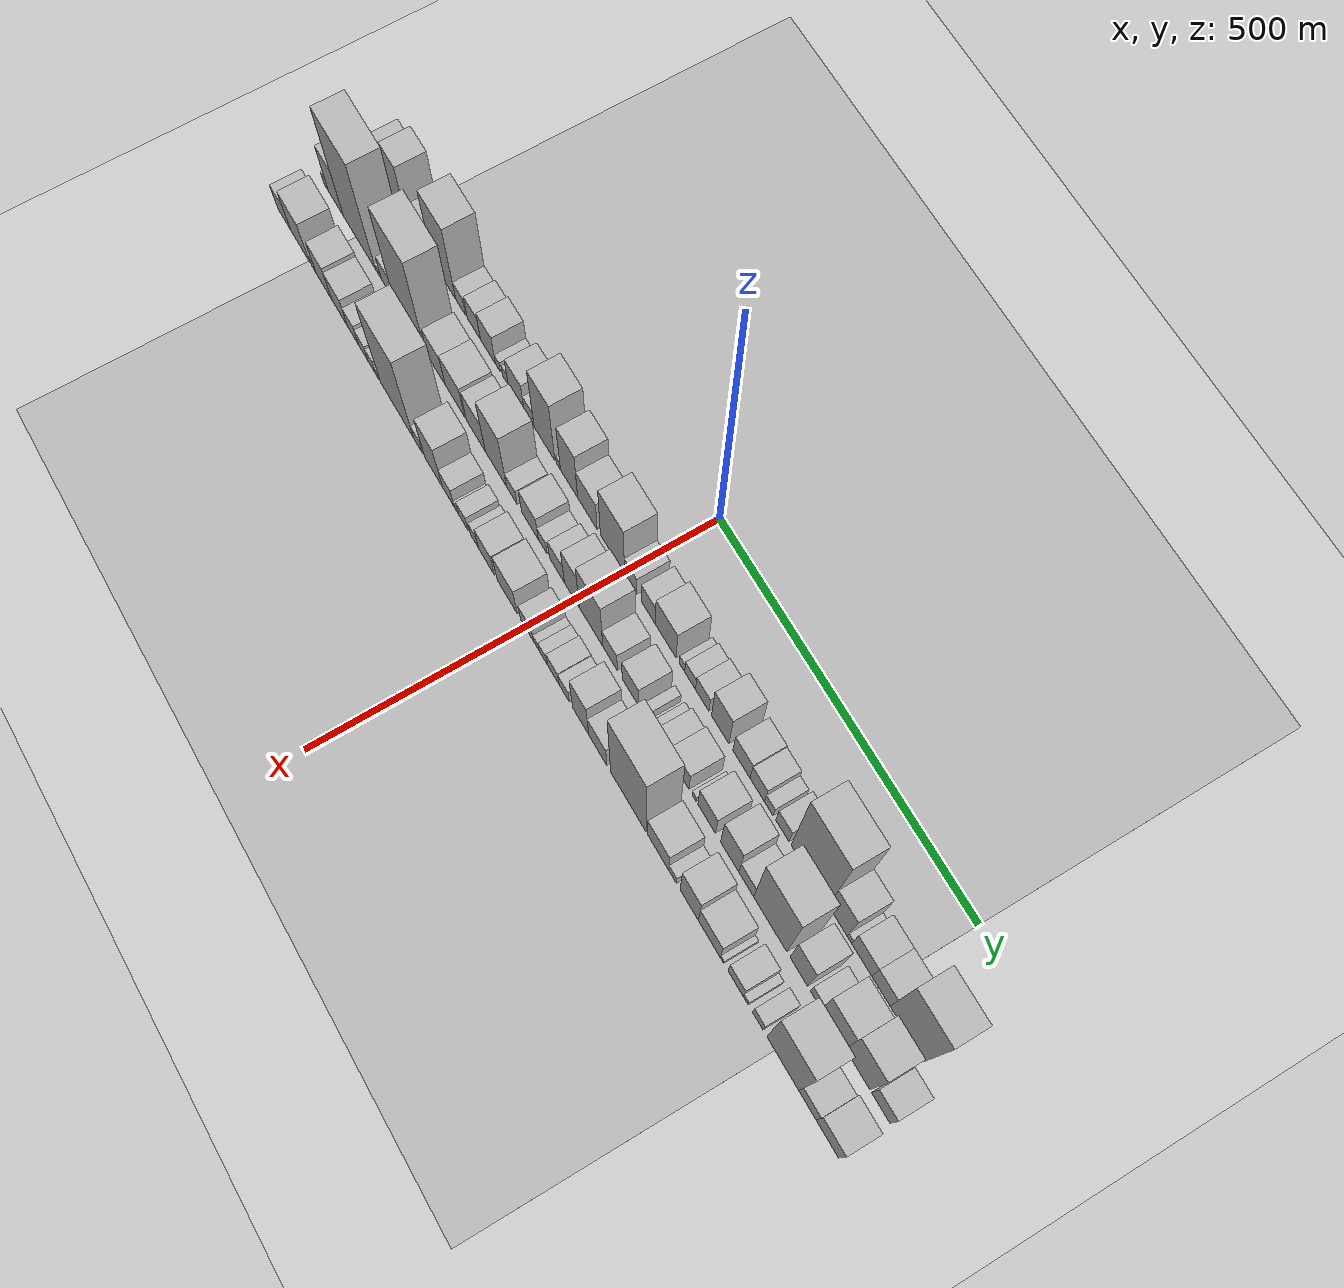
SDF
<?xml version="1.0" encoding="utf-8"?>

<sdf version="1.6">

   <world name="default">

      <gui fullscreen="0">

         <camera name="user_camera">

            <pose>-15 0 4.57585 0 0 0</pose>

            <view_controller>orbit</view_controller>

         </camera>

      </gui>

      <scene>

         <sky>

           <clouds>

             <speed>12</speed>

           </clouds>

         </sky>

         <ambient>0.4 0.4 0.4 1</ambient>

         <background>0.7 0.7 0.7 1</background>

         <shadows>1</shadows>

      </scene>

      <gravity>0 0 -9.8066</gravity>

      <magnetic_field>6e-06 2.3e-05 -4.2e-05</magnetic_field>

      <physics default="0" name="default_physics" type="ode">

         <ode>

            <solver>

               <type>quick</type>

               <iters>10</iters>

               <sor>1.0</sor>

               <use_dynamic_moi_rescaling>0</use_dynamic_moi_rescaling>

            </solver>

            <constraints>

               <cfm>0</cfm>

               <erp>0.2</erp>

               <contact_max_correcting_vel>100</contact_max_correcting_vel>

               <contact_surface_layer>0.001</contact_surface_layer>

            </constraints>

         </ode>

         <max_step_size>0.004</max_step_size>

         <real_time_factor>1</real_time_factor>

         <real_time_update_rate>250</real_time_update_rate>

      </physics>

      <light name="sun" type="directional">

         <cast_shadows>1</cast_shadows>

         <pose>0 0 10 0 0 0</pose>

         <diffuse>0.8 0.8 0.8 1</diffuse>

         <specular>0.2 0.2 0.2 1</specular>

         <attenuation>

            <range>1000</range>

            <constant>0.9</constant>

            <linear>0.01</linear>

            <quadratic>0.001</quadratic>

         </attenuation>

         <direction>-0.5 0.1 -0.9</direction>

      </light>

      <include>

         <name>ground_plane_1</name>

         <uri>model://HANNAS_ground_plane</uri>

         <pose>0 0 0  0 0 0</pose>

      </include>

      <include>

         <name>ground_plane_2</name>

         <uri>model://HANNAS_ground_plane</uri>

         <pose>100 0 0  0 0 0</pose>

      </include>

      <model name="building_1">

         <static>1</static>

         <pose frame="">100.0000 -549.5142 0 0.000000 0.000000 0.000000</pose>

         <link name="link">

            <pose frame="">0 0 34.50 0 0 0</pose>

            <collision name="collision">

               <geometry>

                  <box>

                     <size>40.0000 40.9715 69.0000</size>

                  </box>

               </geometry>

               <max_contacts>10</max_contacts>

               <surface>

                  <contact>

                     <ode/>

                  </contact>

                  <bounce/>

                  <friction>

                     <torsional>

                        <ode/>

                     </torsional>

                     <ode/>

                  </friction>

               </surface>

            </collision>

            <visual name="visual">

               <cast_shadows>0</cast_shadows>

               <geometry>

                  <box>

                     <size>40.0000 40.9715 69.0000</size>

                  </box>

               </geometry>

               <material>

                  <script>

                     <uri>model://HANNAS_wall/materials/scripts</uri>

                     <uri>model://HANNAS_wall/materials/textures</uri>

                     <name>vrc/HANNAS_wall</name>

                  </script>

               </material>

            </visual>

            <self_collide>0</self_collide>

            <enable_wind>0</enable_wind>

            <kinematic>0</kinematic>

         </link>

      </model>

      <model name="building_2">

         <static>1</static>

         <pose frame="">100.0000 -510.6630 0 0.000000 0.000000 0.000000</pose>

         <link name="link">

            <pose frame="">0 0 55.50 0 0 0</pose>

            <collision name="collision">

               <geometry>

                  <box>

                     <size>40.0000 36.7310 111.0000</size>

                  </box>

               </geometry>

               <max_contacts>10</max_contacts>

               <surface>

                  <contact>

                     <ode/>

                  </contact>

                  <bounce/>

                  <friction>

                     <torsional>

                        <ode/>

                     </torsional>

                     <ode/>

                  </friction>

               </surface>

            </collision>

            <visual name="visual">

               <cast_shadows>0</cast_shadows>

               <geometry>

                  <box>

                     <size>40.0000 36.7310 111.0000</size>

                  </box>

               </geometry>

               <material>

                  <script>

                     <uri>model://HANNAS_wall/materials/scripts</uri>

                     <uri>model://HANNAS_wall/materials/textures</uri>

                     <name>vrc/HANNAS_wall</name>

                  </script>

               </material>

            </visual>

            <self_collide>0</self_collide>

            <enable_wind>0</enable_wind>

            <kinematic>0</kinematic>

         </link>

      </model>

      <model name="building_3">

         <static>1</static>

         <pose frame="">100.0000 -479.3074 0 0.000000 0.000000 0.000000</pose>

         <link name="link">

            <pose frame="">0 0 16.50 0 0 0</pose>

            <collision name="collision">

               <geometry>

                  <box>

                     <size>40.0000 17.9802 33.0000</size>

                  </box>

               </geometry>

               <max_contacts>10</max_contacts>

               <surface>

                  <contact>

                     <ode/>

                  </contact>

                  <bounce/>

                  <friction>

                     <torsional>

                        <ode/>

                     </torsional>

                     <ode/>

                  </friction>

               </surface>

            </collision>

            <visual name="visual">

               <cast_shadows>0</cast_shadows>

               <geometry>

                  <box>

                     <size>40.0000 17.9802 33.0000</size>

                  </box>

               </geometry>

               <material>

                  <script>

                     <uri>model://HANNAS_wall/materials/scripts</uri>

                     <uri>model://HANNAS_wall/materials/textures</uri>

                     <name>vrc/HANNAS_wall</name>

                  </script>

               </material>

            </visual>

            <self_collide>0</self_collide>

            <enable_wind>0</enable_wind>

            <kinematic>0</kinematic>

         </link>

      </model>

      <model name="building_4">

         <static>1</static>

         <pose frame="">100.0000 -446.9701 0 0.000000 0.000000 0.000000</pose>

         <link name="link">

            <pose frame="">0 0 37.50 0 0 0</pose>

            <collision name="collision">

               <geometry>

                  <box>

                     <size>40.0000 38.6944 75.0000</size>

                  </box>

               </geometry>

               <max_contacts>10</max_contacts>

               <surface>

                  <contact>

                     <ode/>

                  </contact>

                  <bounce/>

                  <friction>

                     <torsional>

                        <ode/>

                     </torsional>

                     <ode/>

                  </friction>

               </surface>

            </collision>

            <visual name="visual">

               <cast_shadows>0</cast_shadows>

               <geometry>

                  <box>

                     <size>40.0000 38.6944 75.0000</size>

                  </box>

               </geometry>

               <material>

                  <script>

                     <uri>model://HANNAS_wall/materials/scripts</uri>

                     <uri>model://HANNAS_wall/materials/textures</uri>

                     <name>vrc/HANNAS_wall</name>

                  </script>

               </material>

            </visual>

            <self_collide>0</self_collide>

            <enable_wind>0</enable_wind>

            <kinematic>0</kinematic>

         </link>

      </model>

      <model name="building_5">

         <static>1</static>

         <pose frame="">100.0000 -400.6949 0 0.000000 0.000000 0.000000</pose>

         <link name="link">

            <pose frame="">0 0 79.50 0 0 0</pose>

            <collision name="collision">

               <geometry>

                  <box>

                     <size>40.0000 53.8561 159.0000</size>

                  </box>

               </geometry>

               <max_contacts>10</max_contacts>

               <surface>

                  <contact>

                     <ode/>

                  </contact>

                  <bounce/>

                  <friction>

                     <torsional>

                        <ode/>

                     </torsional>

                     <ode/>

                  </friction>

               </surface>

            </collision>

            <visual name="visual">

               <cast_shadows>0</cast_shadows>

               <geometry>

                  <box>

                     <size>40.0000 53.8561 159.0000</size>

                  </box>

               </geometry>

               <material>

                  <script>

                     <uri>model://HANNAS_wall/materials/scripts</uri>

                     <uri>model://HANNAS_wall/materials/textures</uri>

                     <name>vrc/HANNAS_wall</name>

                  </script>

               </material>

            </visual>

            <self_collide>0</self_collide>

            <enable_wind>0</enable_wind>

            <kinematic>0</kinematic>

         </link>

      </model>

      <model name="building_6">

         <static>1</static>

         <pose frame="">100.0000 -362.1579 0 0.000000 0.000000 0.000000</pose>

         <link name="link">

            <pose frame="">0 0 21.00 0 0 0</pose>

            <collision name="collision">

               <geometry>

                  <box>

                     <size>40.0000 23.2179 42.0000</size>

                  </box>

               </geometry>

               <max_contacts>10</max_contacts>

               <surface>

                  <contact>

                     <ode/>

                  </contact>

                  <bounce/>

                  <friction>

                     <torsional>

                        <ode/>

                     </torsional>

                     <ode/>

                  </friction>

               </surface>

            </collision>

            <visual name="visual">

               <cast_shadows>0</cast_shadows>

               <geometry>

                  <box>

                     <size>40.0000 23.2179 42.0000</size>

                  </box>

               </geometry>

               <material>

                  <script>

                     <uri>model://HANNAS_wall/materials/scripts</uri>

                     <uri>model://HANNAS_wall/materials/textures</uri>

                     <name>vrc/HANNAS_wall</name>

                  </script>

               </material>

            </visual>

            <self_collide>0</self_collide>

            <enable_wind>0</enable_wind>

            <kinematic>0</kinematic>

         </link>

      </model>

      <model name="building_7">

         <static>1</static>

         <pose frame="">100.0000 -331.3385 0 0.000000 0.000000 0.000000</pose>

         <link name="link">

            <pose frame="">0 0 27.00 0 0 0</pose>

            <collision name="collision">

               <geometry>

                  <box>

                     <size>40.0000 30.4209 54.0000</size>

                  </box>

               </geometry>

               <max_contacts>10</max_contacts>

               <surface>

                  <contact>

                     <ode/>

                  </contact>

                  <bounce/>

                  <friction>

                     <torsional>

                        <ode/>

                     </torsional>

                     <ode/>

                  </friction>

               </surface>

            </collision>

            <visual name="visual">

               <cast_shadows>0</cast_shadows>

               <geometry>

                  <box>

                     <size>40.0000 30.4209 54.0000</size>

                  </box>

               </geometry>

               <material>

                  <script>

                     <uri>model://HANNAS_wall/materials/scripts</uri>

                     <uri>model://HANNAS_wall/materials/textures</uri>

                     <name>vrc/HANNAS_wall</name>

                  </script>

               </material>

            </visual>

            <self_collide>0</self_collide>

            <enable_wind>0</enable_wind>

            <kinematic>0</kinematic>

         </link>

      </model>

      <model name="building_8">

         <static>1</static>

         <pose frame="">100.0000 -299.0289 0 0.000000 0.000000 0.000000</pose>

         <link name="link">

            <pose frame="">0 0 33.00 0 0 0</pose>

            <collision name="collision">

               <geometry>

                  <box>

                     <size>40.0000 34.1982 66.0000</size>

                  </box>

               </geometry>

               <max_contacts>10</max_contacts>

               <surface>

                  <contact>

                     <ode/>

                  </contact>

                  <bounce/>

                  <friction>

                     <torsional>

                        <ode/>

                     </torsional>

                     <ode/>

                  </friction>

               </surface>

            </collision>

            <visual name="visual">

               <cast_shadows>0</cast_shadows>

               <geometry>

                  <box>

                     <size>40.0000 34.1982 66.0000</size>

                  </box>

               </geometry>

               <material>

                  <script>

                     <uri>model://HANNAS_wall/materials/scripts</uri>

                     <uri>model://HANNAS_wall/materials/textures</uri>

                     <name>vrc/HANNAS_wall</name>

                  </script>

               </material>

            </visual>

            <self_collide>0</self_collide>

            <enable_wind>0</enable_wind>

            <kinematic>0</kinematic>

         </link>

      </model>

      <model name="building_9">

         <static>1</static>

         <pose frame="">100.0000 -276.3239 0 0.000000 0.000000 0.000000</pose>

         <link name="link">

            <pose frame="">0 0 12.00 0 0 0</pose>

            <collision name="collision">

               <geometry>

                  <box>

                     <size>40.0000 11.2118 24.0000</size>

                  </box>

               </geometry>

               <max_contacts>10</max_contacts>

               <surface>

                  <contact>

                     <ode/>

                  </contact>

                  <bounce/>

                  <friction>

                     <torsional>

                        <ode/>

                     </torsional>

                     <ode/>

                  </friction>

               </surface>

            </collision>

            <visual name="visual">

               <cast_shadows>0</cast_shadows>

               <geometry>

                  <box>

                     <size>40.0000 11.2118 24.0000</size>

                  </box>

               </geometry>

               <material>

                  <script>

                     <uri>model://HANNAS_wall/materials/scripts</uri>

                     <uri>model://HANNAS_wall/materials/textures</uri>

                     <name>vrc/HANNAS_wall</name>

                  </script>

               </material>

            </visual>

            <self_collide>0</self_collide>

            <enable_wind>0</enable_wind>

            <kinematic>0</kinematic>

         </link>

      </model>

      <model name="building_10">

         <static>1</static>

         <pose frame="">100.0000 -259.2312 0 0.000000 0.000000 0.000000</pose>

         <link name="link">

            <pose frame="">0 0 13.50 0 0 0</pose>

            <collision name="collision">

               <geometry>

                  <box>

                     <size>40.0000 12.9735 27.0000</size>

                  </box>

               </geometry>

               <max_contacts>10</max_contacts>

               <surface>

                  <contact>

                     <ode/>

                  </contact>

                  <bounce/>

                  <friction>

                     <torsional>

                        <ode/>

                     </torsional>

                     <ode/>

                  </friction>

               </surface>

            </collision>

            <visual name="visual">

               <cast_shadows>0</cast_shadows>

               <geometry>

                  <box>

                     <size>40.0000 12.9735 27.0000</size>

                  </box>

               </geometry>

               <material>

                  <script>

                     <uri>model://HANNAS_wall/materials/scripts</uri>

                     <uri>model://HANNAS_wall/materials/textures</uri>

                     <name>vrc/HANNAS_wall</name>

                  </script>

               </material>

            </visual>

            <self_collide>0</self_collide>

            <enable_wind>0</enable_wind>

            <kinematic>0</kinematic>

         </link>

      </model>

      <model name="building_11">

         <static>1</static>

         <pose frame="">100.0000 -234.8249 0 0.000000 0.000000 0.000000</pose>

         <link name="link">

            <pose frame="">0 0 33.00 0 0 0</pose>

            <collision name="collision">

               <geometry>

                  <box>

                     <size>40.0000 35.8391 66.0000</size>

                  </box>

               </geometry>

               <max_contacts>10</max_contacts>

               <surface>

                  <contact>

                     <ode/>

                  </contact>

                  <bounce/>

                  <friction>

                     <torsional>

                        <ode/>

                     </torsional>

                     <ode/>

                  </friction>

               </surface>

            </collision>

            <visual name="visual">

               <cast_shadows>0</cast_shadows>

               <geometry>

                  <box>

                     <size>40.0000 35.8391 66.0000</size>

                  </box>

               </geometry>

               <material>

                  <script>

                     <uri>model://HANNAS_wall/materials/scripts</uri>

                     <uri>model://HANNAS_wall/materials/textures</uri>

                     <name>vrc/HANNAS_wall</name>

                  </script>

               </material>

            </visual>

            <self_collide>0</self_collide>

            <enable_wind>0</enable_wind>

            <kinematic>0</kinematic>

         </link>

      </model>

      <model name="building_12">

         <static>1</static>

         <pose frame="">100.0000 -205.6137 0 0.000000 0.000000 0.000000</pose>

         <link name="link">

            <pose frame="">0 0 19.50 0 0 0</pose>

            <collision name="collision">

               <geometry>

                  <box>

                     <size>40.0000 22.5834 39.0000</size>

                  </box>

               </geometry>

               <max_contacts>10</max_contacts>

               <surface>

                  <contact>

                     <ode/>

                  </contact>

                  <bounce/>

                  <friction>

                     <torsional>

                        <ode/>

                     </torsional>

                     <ode/>

                  </friction>

               </surface>

            </collision>

            <visual name="visual">

               <cast_shadows>0</cast_shadows>

               <geometry>

                  <box>

                     <size>40.0000 22.5834 39.0000</size>

                  </box>

               </geometry>

               <material>

                  <script>

                     <uri>model://HANNAS_wall/materials/scripts</uri>

                     <uri>model://HANNAS_wall/materials/textures</uri>

                     <name>vrc/HANNAS_wall</name>

                  </script>

               </material>

            </visual>

            <self_collide>0</self_collide>

            <enable_wind>0</enable_wind>

            <kinematic>0</kinematic>

         </link>

      </model>

      <model name="building_13">

         <static>1</static>

         <pose frame="">100.0000 -171.4702 0 0.000000 0.000000 0.000000</pose>

         <link name="link">

            <pose frame="">0 0 73.50 0 0 0</pose>

            <collision name="collision">

               <geometry>

                  <box>

                     <size>40.0000 45.7037 147.0000</size>

                  </box>

               </geometry>

               <max_contacts>10</max_contacts>

               <surface>

                  <contact>

                     <ode/>

                  </contact>

                  <bounce/>

                  <friction>

                     <torsional>

                        <ode/>

                     </torsional>

                     <ode/>

                  </friction>

               </surface>

            </collision>

            <visual name="visual">

               <cast_shadows>0</cast_shadows>

               <geometry>

                  <box>

                     <size>40.0000 45.7037 147.0000</size>

                  </box>

               </geometry>

               <material>

                  <script>

                     <uri>model://HANNAS_wall/materials/scripts</uri>

                     <uri>model://HANNAS_wall/materials/textures</uri>

                     <name>vrc/HANNAS_wall</name>

                  </script>

               </material>

            </visual>

            <self_collide>0</self_collide>

            <enable_wind>0</enable_wind>

            <kinematic>0</kinematic>

         </link>

      </model>

      <model name="building_14">

         <static>1</static>

         <pose frame="">100.0000 -140.9780 0 0.000000 0.000000 0.000000</pose>

         <link name="link">

            <pose frame="">0 0 10.50 0 0 0</pose>

            <collision name="collision">

               <geometry>

                  <box>

                     <size>40.0000 9.2807 21.0000</size>

                  </box>

               </geometry>

               <max_contacts>10</max_contacts>

               <surface>

                  <contact>

                     <ode/>

                  </contact>

                  <bounce/>

                  <friction>

                     <torsional>

                        <ode/>

                     </torsional>

                     <ode/>

                  </friction>

               </surface>

            </collision>

            <visual name="visual">

               <cast_shadows>0</cast_shadows>

               <geometry>

                  <box>

                     <size>40.0000 9.2807 21.0000</size>

                  </box>

               </geometry>

               <material>

                  <script>

                     <uri>model://HANNAS_wall/materials/scripts</uri>

                     <uri>model://HANNAS_wall/materials/textures</uri>

                     <name>vrc/HANNAS_wall</name>

                  </script>

               </material>

            </visual>

            <self_collide>0</self_collide>

            <enable_wind>0</enable_wind>

            <kinematic>0</kinematic>

         </link>

      </model>

      <model name="building_15">

         <static>1</static>

         <pose frame="">100.0000 -117.5047 0 0.000000 0.000000 0.000000</pose>

         <link name="link">

            <pose frame="">0 0 58.50 0 0 0</pose>

            <collision name="collision">

               <geometry>

                  <box>

                     <size>40.0000 37.6661 117.0000</size>

                  </box>

               </geometry>

               <max_contacts>10</max_contacts>

               <surface>

                  <contact>

                     <ode/>

                  </contact>

                  <bounce/>

                  <friction>

                     <torsional>

                        <ode/>

                     </torsional>

                     <ode/>

                  </friction>

               </surface>

            </collision>

            <visual name="visual">

               <cast_shadows>0</cast_shadows>

               <geometry>

                  <box>

                     <size>40.0000 37.6661 117.0000</size>

                  </box>

               </geometry>

               <material>

                  <script>

                     <uri>model://HANNAS_wall/materials/scripts</uri>

                     <uri>model://HANNAS_wall/materials/textures</uri>

                     <name>vrc/HANNAS_wall</name>

                  </script>

               </material>

            </visual>

            <self_collide>0</self_collide>

            <enable_wind>0</enable_wind>

            <kinematic>0</kinematic>

         </link>

      </model>

      <model name="building_16">

         <static>1</static>

         <pose frame="">100.0000 -77.7302 0 0.000000 0.000000 0.000000</pose>

         <link name="link">

            <pose frame="">0 0 37.50 0 0 0</pose>

            <collision name="collision">

               <geometry>

                  <box>

                     <size>40.0000 41.8828 75.0000</size>

                  </box>

               </geometry>

               <max_contacts>10</max_contacts>

               <surface>

                  <contact>

                     <ode/>

                  </contact>

                  <bounce/>

                  <friction>

                     <torsional>

                        <ode/>

                     </torsional>

                     <ode/>

                  </friction>

               </surface>

            </collision>

            <visual name="visual">

               <cast_shadows>0</cast_shadows>

               <geometry>

                  <box>

                     <size>40.0000 41.8828 75.0000</size>

                  </box>

               </geometry>

               <material>

                  <script>

                     <uri>model://HANNAS_wall/materials/scripts</uri>

                     <uri>model://HANNAS_wall/materials/textures</uri>

                     <name>vrc/HANNAS_wall</name>

                  </script>

               </material>

            </visual>

            <self_collide>0</self_collide>

            <enable_wind>0</enable_wind>

            <kinematic>0</kinematic>

         </link>

      </model>

      <model name="building_17">

         <static>1</static>

         <pose frame="">100.0000 -24.1237 0 0.000000 0.000000 0.000000</pose>

         <link name="link">

            <pose frame="">0 0 66.00 0 0 0</pose>

            <collision name="collision">

               <geometry>

                  <box>

                     <size>40.0000 51.3303 132.0000</size>

                  </box>

               </geometry>

               <max_contacts>10</max_contacts>

               <surface>

                  <contact>

                     <ode/>

                  </contact>

                  <bounce/>

                  <friction>

                     <torsional>

                        <ode/>

                     </torsional>

                     <ode/>

                  </friction>

               </surface>

            </collision>

            <visual name="visual">

               <cast_shadows>0</cast_shadows>

               <geometry>

                  <box>

                     <size>40.0000 51.3303 132.0000</size>

                  </box>

               </geometry>

               <material>

                  <script>

                     <uri>model://HANNAS_wall/materials/scripts</uri>

                     <uri>model://HANNAS_wall/materials/textures</uri>

                     <name>vrc/HANNAS_wall</name>

                  </script>

               </material>

            </visual>

            <self_collide>0</self_collide>

            <enable_wind>0</enable_wind>

            <kinematic>0</kinematic>

         </link>

      </model>

      <model name="building_18">

         <static>1</static>

         <pose frame="">100.0000 14.7104 0 0.000000 0.000000 0.000000</pose>

         <link name="link">

            <pose frame="">0 0 25.50 0 0 0</pose>

            <collision name="collision">

               <geometry>

                  <box>

                     <size>40.0000 26.3379 51.0000</size>

                  </box>

               </geometry>

               <max_contacts>10</max_contacts>

               <surface>

                  <contact>

                     <ode/>

                  </contact>

                  <bounce/>

                  <friction>

                     <torsional>

                        <ode/>

                     </torsional>

                     <ode/>

                  </friction>

               </surface>

            </collision>

            <visual name="visual">

               <cast_shadows>0</cast_shadows>

               <geometry>

                  <box>

                     <size>40.0000 26.3379 51.0000</size>

                  </box>

               </geometry>

               <material>

                  <script>

                     <uri>model://HANNAS_wall/materials/scripts</uri>

                     <uri>model://HANNAS_wall/materials/textures</uri>

                     <name>vrc/HANNAS_wall</name>

                  </script>

               </material>

            </visual>

            <self_collide>0</self_collide>

            <enable_wind>0</enable_wind>

            <kinematic>0</kinematic>

         </link>

      </model>

      <model name="building_19">

         <static>1</static>

         <pose frame="">100.0000 51.6035 0 0.000000 0.000000 0.000000</pose>

         <link name="link">

            <pose frame="">0 0 28.50 0 0 0</pose>

            <collision name="collision">

               <geometry>

                  <box>

                     <size>40.0000 29.4482 57.0000</size>

                  </box>

               </geometry>

               <max_contacts>10</max_contacts>

               <surface>

                  <contact>

                     <ode/>

                  </contact>

                  <bounce/>

                  <friction>

                     <torsional>

                        <ode/>

                     </torsional>

                     <ode/>

                  </friction>

               </surface>

            </collision>

            <visual name="visual">

               <cast_shadows>0</cast_shadows>

               <geometry>

                  <box>

                     <size>40.0000 29.4482 57.0000</size>

                  </box>

               </geometry>

               <material>

                  <script>

                     <uri>model://HANNAS_wall/materials/scripts</uri>

                     <uri>model://HANNAS_wall/materials/textures</uri>

                     <name>vrc/HANNAS_wall</name>

                  </script>

               </material>

            </visual>

            <self_collide>0</self_collide>

            <enable_wind>0</enable_wind>

            <kinematic>0</kinematic>

         </link>

      </model>

      <model name="building_20">

         <static>1</static>

         <pose frame="">100.0000 87.7488 0 0.000000 0.000000 0.000000</pose>

         <link name="link">

            <pose frame="">0 0 42.00 0 0 0</pose>

            <collision name="collision">

               <geometry>

                  <box>

                     <size>40.0000 42.8424 84.0000</size>

                  </box>

               </geometry>

               <max_contacts>10</max_contacts>

               <surface>

                  <contact>

                     <ode/>

                  </contact>

                  <bounce/>

                  <friction>

                     <torsional>

                        <ode/>

                     </torsional>

                     <ode/>

                  </friction>

               </surface>

            </collision>

            <visual name="visual">

               <cast_shadows>0</cast_shadows>

               <geometry>

                  <box>

                     <size>40.0000 42.8424 84.0000</size>

                  </box>

               </geometry>

               <material>

                  <script>

                     <uri>model://HANNAS_wall/materials/scripts</uri>

                     <uri>model://HANNAS_wall/materials/textures</uri>

                     <name>vrc/HANNAS_wall</name>

                  </script>

               </material>

            </visual>

            <self_collide>0</self_collide>

            <enable_wind>0</enable_wind>

            <kinematic>0</kinematic>

         </link>

      </model>

      <model name="building_21">

         <static>1</static>

         <pose frame="">100.0000 120.8142 0 0.000000 0.000000 0.000000</pose>

         <link name="link">

            <pose frame="">0 0 13.50 0 0 0</pose>

            <collision name="collision">

               <geometry>

                  <box>

                     <size>40.0000 11.2885 27.0000</size>

                  </box>

               </geometry>

               <max_contacts>10</max_contacts>

               <surface>

                  <contact>

                     <ode/>

                  </contact>

                  <bounce/>

                  <friction>

                     <torsional>

                        <ode/>

                     </torsional>

                     <ode/>

                  </friction>

               </surface>

            </collision>

            <visual name="visual">

               <cast_shadows>0</cast_shadows>

               <geometry>

                  <box>

                     <size>40.0000 11.2885 27.0000</size>

                  </box>

               </geometry>

               <material>

                  <script>

                     <uri>model://HANNAS_wall/materials/scripts</uri>

                     <uri>model://HANNAS_wall/materials/textures</uri>

                     <name>vrc/HANNAS_wall</name>

                  </script>

               </material>

            </visual>

            <self_collide>0</self_collide>

            <enable_wind>0</enable_wind>

            <kinematic>0</kinematic>

         </link>

      </model>

      <model name="building_22">

         <static>1</static>

         <pose frame="">100.0000 137.4908 0 0.000000 0.000000 0.000000</pose>

         <link name="link">

            <pose frame="">0 0 19.50 0 0 0</pose>

            <collision name="collision">

               <geometry>

                  <box>

                     <size>40.0000 22.0646 39.0000</size>

                  </box>

               </geometry>

               <max_contacts>10</max_contacts>

               <surface>

                  <contact>

                     <ode/>

                  </contact>

                  <bounce/>

                  <friction>

                     <torsional>

                        <ode/>

                     </torsional>

                     <ode/>

                  </friction>

               </surface>

            </collision>

            <visual name="visual">

               <cast_shadows>0</cast_shadows>

               <geometry>

                  <box>

                     <size>40.0000 22.0646 39.0000</size>

                  </box>

               </geometry>

               <material>

                  <script>

                     <uri>model://HANNAS_wall/materials/scripts</uri>

                     <uri>model://HANNAS_wall/materials/textures</uri>

                     <name>vrc/HANNAS_wall</name>

                  </script>

               </material>

            </visual>

            <self_collide>0</self_collide>

            <enable_wind>0</enable_wind>

            <kinematic>0</kinematic>

         </link>

      </model>

      <model name="building_23">

         <static>1</static>

         <pose frame="">100.0000 162.0961 0 0.000000 0.000000 0.000000</pose>

         <link name="link">

            <pose frame="">0 0 24.00 0 0 0</pose>

            <collision name="collision">

               <geometry>

                  <box>

                     <size>40.0000 27.1462 48.0000</size>

                  </box>

               </geometry>

               <max_contacts>10</max_contacts>

               <surface>

                  <contact>

                     <ode/>

                  </contact>

                  <bounce/>

                  <friction>

                     <torsional>

                        <ode/>

                     </torsional>

                     <ode/>

                  </friction>

               </surface>

            </collision>

            <visual name="visual">

               <cast_shadows>0</cast_shadows>

               <geometry>

                  <box>

                     <size>40.0000 27.1462 48.0000</size>

                  </box>

               </geometry>

               <material>

                  <script>

                     <uri>model://HANNAS_wall/materials/scripts</uri>

                     <uri>model://HANNAS_wall/materials/textures</uri>

                     <name>vrc/HANNAS_wall</name>

                  </script>

               </material>

            </visual>

            <self_collide>0</self_collide>

            <enable_wind>0</enable_wind>

            <kinematic>0</kinematic>

         </link>

      </model>

      <model name="building_24">

         <static>1</static>

         <pose frame="">100.0000 198.0278 0 0.000000 0.000000 0.000000</pose>

         <link name="link">

            <pose frame="">0 0 48.00 0 0 0</pose>

            <collision name="collision">

               <geometry>

                  <box>

                     <size>40.0000 34.7173 96.0000</size>

                  </box>

               </geometry>

               <max_contacts>10</max_contacts>

               <surface>

                  <contact>

                     <ode/>

                  </contact>

                  <bounce/>

                  <friction>

                     <torsional>

                        <ode/>

                     </torsional>

                     <ode/>

                  </friction>

               </surface>

            </collision>

            <visual name="visual">

               <cast_shadows>0</cast_shadows>

               <geometry>

                  <box>

                     <size>40.0000 34.7173 96.0000</size>

                  </box>

               </geometry>

               <material>

                  <script>

                     <uri>model://HANNAS_wall/materials/scripts</uri>

                     <uri>model://HANNAS_wall/materials/textures</uri>

                     <name>vrc/HANNAS_wall</name>

                  </script>

               </material>

            </visual>

            <self_collide>0</self_collide>

            <enable_wind>0</enable_wind>

            <kinematic>0</kinematic>

         </link>

      </model>

      <model name="building_25">

         <static>1</static>

         <pose frame="">100.0000 240.3025 0 0.000000 0.000000 0.000000</pose>

         <link name="link">

            <pose frame="">0 0 30.00 0 0 0</pose>

            <collision name="collision">

               <geometry>

                  <box>

                     <size>40.0000 33.8321 60.0000</size>

                  </box>

               </geometry>

               <max_contacts>10</max_contacts>

               <surface>

                  <contact>

                     <ode/>

                  </contact>

                  <bounce/>

                  <friction>

                     <torsional>

                        <ode/>

                     </torsional>

                     <ode/>

                  </friction>

               </surface>

            </collision>

            <visual name="visual">

               <cast_shadows>0</cast_shadows>

               <geometry>

                  <box>

                     <size>40.0000 33.8321 60.0000</size>

                  </box>

               </geometry>

               <material>

                  <script>

                     <uri>model://HANNAS_wall/materials/scripts</uri>

                     <uri>model://HANNAS_wall/materials/textures</uri>

                     <name>vrc/HANNAS_wall</name>

                  </script>

               </material>

            </visual>

            <self_collide>0</self_collide>

            <enable_wind>0</enable_wind>

            <kinematic>0</kinematic>

         </link>

      </model>

      <model name="building_26">

         <static>1</static>

         <pose frame="">100.0000 271.3772 0 0.000000 0.000000 0.000000</pose>

         <link name="link">

            <pose frame="">0 0 27.00 0 0 0</pose>

            <collision name="collision">

               <geometry>

                  <box>

                     <size>40.0000 28.3173 54.0000</size>

                  </box>

               </geometry>

               <max_contacts>10</max_contacts>

               <surface>

                  <contact>

                     <ode/>

                  </contact>

                  <bounce/>

                  <friction>

                     <torsional>

                        <ode/>

                     </torsional>

                     <ode/>

                  </friction>

               </surface>

            </collision>

            <visual name="visual">

               <cast_shadows>0</cast_shadows>

               <geometry>

                  <box>

                     <size>40.0000 28.3173 54.0000</size>

                  </box>

               </geometry>

               <material>

                  <script>

                     <uri>model://HANNAS_wall/materials/scripts</uri>

                     <uri>model://HANNAS_wall/materials/textures</uri>

                     <name>vrc/HANNAS_wall</name>

                  </script>

               </material>

            </visual>

            <self_collide>0</self_collide>

            <enable_wind>0</enable_wind>

            <kinematic>0</kinematic>

         </link>

      </model>

      <model name="building_27">

         <static>1</static>

         <pose frame="">100.0000 293.9437 0 0.000000 0.000000 0.000000</pose>

         <link name="link">

            <pose frame="">0 0 16.50 0 0 0</pose>

            <collision name="collision">

               <geometry>

                  <box>

                     <size>40.0000 16.8156 33.0000</size>

                  </box>

               </geometry>

               <max_contacts>10</max_contacts>

               <surface>

                  <contact>

                     <ode/>

                  </contact>

                  <bounce/>

                  <friction>

                     <torsional>

                        <ode/>

                     </torsional>

                     <ode/>

                  </friction>

               </surface>

            </collision>

            <visual name="visual">

               <cast_shadows>0</cast_shadows>

               <geometry>

                  <box>

                     <size>40.0000 16.8156 33.0000</size>

                  </box>

               </geometry>

               <material>

                  <script>

                     <uri>model://HANNAS_wall/materials/scripts</uri>

                     <uri>model://HANNAS_wall/materials/textures</uri>

                     <name>vrc/HANNAS_wall</name>

                  </script>

               </material>

            </visual>

            <self_collide>0</self_collide>

            <enable_wind>0</enable_wind>

            <kinematic>0</kinematic>

         </link>

      </model>

      <model name="building_28">

         <static>1</static>

         <pose frame="">100.0000 320.1187 0 0.000000 0.000000 0.000000</pose>

         <link name="link">

            <pose frame="">0 0 24.00 0 0 0</pose>

            <collision name="collision">

               <geometry>

                  <box>

                     <size>40.0000 25.5344 48.0000</size>

                  </box>

               </geometry>

               <max_contacts>10</max_contacts>

               <surface>

                  <contact>

                     <ode/>

                  </contact>

                  <bounce/>

                  <friction>

                     <torsional>

                        <ode/>

                     </torsional>

                     <ode/>

                  </friction>

               </surface>

            </collision>

            <visual name="visual">

               <cast_shadows>0</cast_shadows>

               <geometry>

                  <box>

                     <size>40.0000 25.5344 48.0000</size>

                  </box>

               </geometry>

               <material>

                  <script>

                     <uri>model://HANNAS_wall/materials/scripts</uri>

                     <uri>model://HANNAS_wall/materials/textures</uri>

                     <name>vrc/HANNAS_wall</name>

                  </script>

               </material>

            </visual>

            <self_collide>0</self_collide>

            <enable_wind>0</enable_wind>

            <kinematic>0</kinematic>

         </link>

      </model>

      <model name="building_29">

         <static>1</static>

         <pose frame="">100.0000 372.0678 0 0.000000 0.000000 0.000000</pose>

         <link name="link">

            <pose frame="">0 0 112.50 0 0 0</pose>

            <collision name="collision">

               <geometry>

                  <box>

                     <size>40.0000 70.3638 225.0000</size>

                  </box>

               </geometry>

               <max_contacts>10</max_contacts>

               <surface>

                  <contact>

                     <ode/>

                  </contact>

                  <bounce/>

                  <friction>

                     <torsional>

                        <ode/>

                     </torsional>

                     <ode/>

                  </friction>

               </surface>

            </collision>

            <visual name="visual">

               <cast_shadows>0</cast_shadows>

               <geometry>

                  <box>

                     <size>40.0000 70.3638 225.0000</size>

                  </box>

               </geometry>

               <material>

                  <script>

                     <uri>model://HANNAS_wall/materials/scripts</uri>

                     <uri>model://HANNAS_wall/materials/textures</uri>

                     <name>vrc/HANNAS_wall</name>

                  </script>

               </material>

            </visual>

            <self_collide>0</self_collide>

            <enable_wind>0</enable_wind>

            <kinematic>0</kinematic>

         </link>

      </model>

      <model name="building_30">

         <static>1</static>

         <pose frame="">100.0000 424.9010 0 0.000000 0.000000 0.000000</pose>

         <link name="link">

            <pose frame="">0 0 51.00 0 0 0</pose>

            <collision name="collision">

               <geometry>

                  <box>

                     <size>40.0000 35.3027 102.0000</size>

                  </box>

               </geometry>

               <max_contacts>10</max_contacts>

               <surface>

                  <contact>

                     <ode/>

                  </contact>

                  <bounce/>

                  <friction>

                     <torsional>

                        <ode/>

                     </torsional>

                     <ode/>

                  </friction>

               </surface>

            </collision>

            <visual name="visual">

               <cast_shadows>0</cast_shadows>

               <geometry>

                  <box>

                     <size>40.0000 35.3027 102.0000</size>

                  </box>

               </geometry>

               <material>

                  <script>

                     <uri>model://HANNAS_wall/materials/scripts</uri>

                     <uri>model://HANNAS_wall/materials/textures</uri>

                     <name>vrc/HANNAS_wall</name>

                  </script>

               </material>

            </visual>

            <self_collide>0</self_collide>

            <enable_wind>0</enable_wind>

            <kinematic>0</kinematic>

         </link>

      </model>

      <model name="building_31">

         <static>1</static>

         <pose frame="">100.0000 446.7557 0 0.000000 0.000000 0.000000</pose>

         <link name="link">

            <pose frame="">0 0 10.50 0 0 0</pose>

            <collision name="collision">

               <geometry>

                  <box>

                     <size>40.0000 8.4066 21.0000</size>

                  </box>

               </geometry>

               <max_contacts>10</max_contacts>

               <surface>

                  <contact>

                     <ode/>

                  </contact>

                  <bounce/>

                  <friction>

                     <torsional>

                        <ode/>

                     </torsional>

                     <ode/>

                  </friction>

               </surface>

            </collision>

            <visual name="visual">

               <cast_shadows>0</cast_shadows>

               <geometry>

                  <box>

                     <size>40.0000 8.4066 21.0000</size>

                  </box>

               </geometry>

               <material>

                  <script>

                     <uri>model://HANNAS_wall/materials/scripts</uri>

                     <uri>model://HANNAS_wall/materials/textures</uri>

                     <name>vrc/HANNAS_wall</name>

                  </script>

               </material>

            </visual>

            <self_collide>0</self_collide>

            <enable_wind>0</enable_wind>

            <kinematic>0</kinematic>

         </link>

      </model>

      <model name="building_32">

         <static>1</static>

         <pose frame="">100.0000 469.5664 0 0.000000 0.000000 0.000000</pose>

         <link name="link">

            <pose frame="">0 0 31.50 0 0 0</pose>

            <collision name="collision">

               <geometry>

                  <box>

                     <size>40.0000 37.2149 63.0000</size>

                  </box>

               </geometry>

               <max_contacts>10</max_contacts>

               <surface>

                  <contact>

                     <ode/>

                  </contact>

                  <bounce/>

                  <friction>

                     <torsional>

                        <ode/>

                     </torsional>

                     <ode/>

                  </friction>

               </surface>

            </collision>

            <visual name="visual">

               <cast_shadows>0</cast_shadows>

               <geometry>

                  <box>

                     <size>40.0000 37.2149 63.0000</size>

                  </box>

               </geometry>

               <material>

                  <script>

                     <uri>model://HANNAS_wall/materials/scripts</uri>

                     <uri>model://HANNAS_wall/materials/textures</uri>

                     <name>vrc/HANNAS_wall</name>

                  </script>

               </material>

            </visual>

            <self_collide>0</self_collide>

            <enable_wind>0</enable_wind>

            <kinematic>0</kinematic>

         </link>

      </model>

      <model name="building_33">

         <static>1</static>

         <pose frame="">100.0000 504.7815 0 0.000000 0.000000 0.000000</pose>

         <link name="link">

            <pose frame="">0 0 31.50 0 0 0</pose>

            <collision name="collision">

               <geometry>

                  <box>

                     <size>40.0000 33.2151 63.0000</size>

                  </box>

               </geometry>

               <max_contacts>10</max_contacts>

               <surface>

                  <contact>

                     <ode/>

                  </contact>

                  <bounce/>

                  <friction>

                     <torsional>

                        <ode/>

                     </torsional>

                     <ode/>

                  </friction>

               </surface>

            </collision>

            <visual name="visual">

               <cast_shadows>0</cast_shadows>

               <geometry>

                  <box>

                     <size>40.0000 33.2151 63.0000</size>

                  </box>

               </geometry>

               <material>

                  <script>

                     <uri>model://HANNAS_wall/materials/scripts</uri>

                     <uri>model://HANNAS_wall/materials/textures</uri>

                     <name>vrc/HANNAS_wall</name>

                  </script>

               </material>

            </visual>

            <self_collide>0</self_collide>

            <enable_wind>0</enable_wind>

            <kinematic>0</kinematic>

         </link>

      </model>

      <model name="building_34">

         <static>1</static>

         <pose frame="">100.0000 552.0399 0 0.000000 0.000000 0.000000</pose>

         <link name="link">

            <pose frame="">0 0 91.50 0 0 0</pose>

            <collision name="collision">

               <geometry>

                  <box>

                     <size>40.0000 61.3017 183.0000</size>

                  </box>

               </geometry>

               <max_contacts>10</max_contacts>

               <surface>

                  <contact>

                     <ode/>

                  </contact>

                  <bounce/>

                  <friction>

                     <torsional>

                        <ode/>

                     </torsional>

                     <ode/>

                  </friction>

               </surface>

            </collision>

            <visual name="visual">

               <cast_shadows>0</cast_shadows>

               <geometry>

                  <box>

                     <size>40.0000 61.3017 183.0000</size>

                  </box>

               </geometry>

               <material>

                  <script>

                     <uri>model://HANNAS_wall/materials/scripts</uri>

                     <uri>model://HANNAS_wall/materials/textures</uri>

                     <name>vrc/HANNAS_wall</name>

                  </script>

               </material>

            </visual>

            <self_collide>0</self_collide>

            <enable_wind>0</enable_wind>

            <kinematic>0</kinematic>

         </link>

      </model>

      <model name="building_35">

         <static>1</static>

         <pose frame="">160.0000 -573.9168 0 0.000000 0.000000 0.000000</pose>

         <link name="link">

            <pose frame="">0 0 13.50 0 0 0</pose>

            <collision name="collision">

               <geometry>

                  <box>

                     <size>40.0000 12.1663 27.0000</size>

                  </box>

               </geometry>

               <max_contacts>10</max_contacts>

               <surface>

                  <contact>

                     <ode/>

                  </contact>

                  <bounce/>

                  <friction>

                     <torsional>

                        <ode/>

                     </torsional>

                     <ode/>

                  </friction>

               </surface>

            </collision>

            <visual name="visual">

               <cast_shadows>0</cast_shadows>

               <geometry>

                  <box>

                     <size>40.0000 12.1663 27.0000</size>

                  </box>

               </geometry>

               <material>

                  <script>

                     <uri>model://HANNAS_wall/materials/scripts</uri>

                     <uri>model://HANNAS_wall/materials/textures</uri>

                     <name>vrc/HANNAS_wall</name>

                  </script>

               </material>

            </visual>

            <self_collide>0</self_collide>

            <enable_wind>0</enable_wind>

            <kinematic>0</kinematic>

         </link>

      </model>

      <model name="building_36">

         <static>1</static>

         <pose frame="">160.0000 -549.4034 0 0.000000 0.000000 0.000000</pose>

         <link name="link">

            <pose frame="">0 0 49.50 0 0 0</pose>

            <collision name="collision">

               <geometry>

                  <box>

                     <size>40.0000 36.8605 99.0000</size>

                  </box>

               </geometry>

               <max_contacts>10</max_contacts>

               <surface>

                  <contact>

                     <ode/>

                  </contact>

                  <bounce/>

                  <friction>

                     <torsional>

                        <ode/>

                     </torsional>

                     <ode/>

                  </friction>

               </surface>

            </collision>

            <visual name="visual">

               <cast_shadows>0</cast_shadows>

               <geometry>

                  <box>

                     <size>40.0000 36.8605 99.0000</size>

                  </box>

               </geometry>

               <material>

                  <script>

                     <uri>model://HANNAS_wall/materials/scripts</uri>

                     <uri>model://HANNAS_wall/materials/textures</uri>

                     <name>vrc/HANNAS_wall</name>

                  </script>

               </material>

            </visual>

            <self_collide>0</self_collide>

            <enable_wind>0</enable_wind>

            <kinematic>0</kinematic>

         </link>

      </model>

      <model name="building_37">

         <static>1</static>

         <pose frame="">160.0000 -491.6236 0 0.000000 0.000000 0.000000</pose>

         <link name="link">

            <pose frame="">0 0 112.50 0 0 0</pose>

            <collision name="collision">

               <geometry>

                  <box>

                     <size>40.0000 78.6990 225.0000</size>

                  </box>

               </geometry>

               <max_contacts>10</max_contacts>

               <surface>

                  <contact>

                     <ode/>

                  </contact>

                  <bounce/>

                  <friction>

                     <torsional>

                        <ode/>

                     </torsional>

                     <ode/>

                  </friction>

               </surface>

            </collision>

            <visual name="visual">

               <cast_shadows>0</cast_shadows>

               <geometry>

                  <box>

                     <size>40.0000 78.6990 225.0000</size>

                  </box>

               </geometry>

               <material>

                  <script>

                     <uri>model://HANNAS_wall/materials/scripts</uri>

                     <uri>model://HANNAS_wall/materials/textures</uri>

                     <name>vrc/HANNAS_wall</name>

                  </script>

               </material>

            </visual>

            <self_collide>0</self_collide>

            <enable_wind>0</enable_wind>

            <kinematic>0</kinematic>

         </link>

      </model>

      <model name="building_38">

         <static>1</static>

         <pose frame="">160.0000 -448.5297 0 0.000000 0.000000 0.000000</pose>

         <link name="link">

            <pose frame="">0 0 7.50 0 0 0</pose>

            <collision name="collision">

               <geometry>

                  <box>

                     <size>40.0000 7.4889 15.0000</size>

                  </box>

               </geometry>

               <max_contacts>10</max_contacts>

               <surface>

                  <contact>

                     <ode/>

                  </contact>

                  <bounce/>

                  <friction>

                     <torsional>

                        <ode/>

                     </torsional>

                     <ode/>

                  </friction>

               </surface>

            </collision>

            <visual name="visual">

               <cast_shadows>0</cast_shadows>

               <geometry>

                  <box>

                     <size>40.0000 7.4889 15.0000</size>

                  </box>

               </geometry>

               <material>

                  <script>

                     <uri>model://HANNAS_wall/materials/scripts</uri>

                     <uri>model://HANNAS_wall/materials/textures</uri>

                     <name>vrc/HANNAS_wall</name>

                  </script>

               </material>

            </visual>

            <self_collide>0</self_collide>

            <enable_wind>0</enable_wind>

            <kinematic>0</kinematic>

         </link>

      </model>

      <model name="building_39">

         <static>1</static>

         <pose frame="">160.0000 -441.5887 0 0.000000 0.000000 0.000000</pose>

         <link name="link">

            <pose frame="">0 0 7.50 0 0 0</pose>

            <collision name="collision">

               <geometry>

                  <box>

                     <size>40.0000 6.3932 15.0000</size>

                  </box>

               </geometry>

               <max_contacts>10</max_contacts>

               <surface>

                  <contact>

                     <ode/>

                  </contact>

                  <bounce/>

                  <friction>

                     <torsional>

                        <ode/>

                     </torsional>

                     <ode/>

                  </friction>

               </surface>

            </collision>

            <visual name="visual">

               <cast_shadows>0</cast_shadows>

               <geometry>

                  <box>

                     <size>40.0000 6.3932 15.0000</size>

                  </box>

               </geometry>

               <material>

                  <script>

                     <uri>model://HANNAS_wall/materials/scripts</uri>

                     <uri>model://HANNAS_wall/materials/textures</uri>

                     <name>vrc/HANNAS_wall</name>

                  </script>

               </material>

            </visual>

            <self_collide>0</self_collide>

            <enable_wind>0</enable_wind>

            <kinematic>0</kinematic>

         </link>

      </model>

      <model name="building_40">

         <static>1</static>

         <pose frame="">160.0000 -423.5004 0 0.000000 0.000000 0.000000</pose>

         <link name="link">

            <pose frame="">0 0 27.00 0 0 0</pose>

            <collision name="collision">

               <geometry>

                  <box>

                     <size>40.0000 29.7834 54.0000</size>

                  </box>

               </geometry>

               <max_contacts>10</max_contacts>

               <surface>

                  <contact>

                     <ode/>

                  </contact>

                  <bounce/>

                  <friction>

                     <torsional>

                        <ode/>

                     </torsional>

                     <ode/>

                  </friction>

               </surface>

            </collision>

            <visual name="visual">

               <cast_shadows>0</cast_shadows>

               <geometry>

                  <box>

                     <size>40.0000 29.7834 54.0000</size>

                  </box>

               </geometry>

               <material>

                  <script>

                     <uri>model://HANNAS_wall/materials/scripts</uri>

                     <uri>model://HANNAS_wall/materials/textures</uri>

                     <name>vrc/HANNAS_wall</name>

                  </script>

               </material>

            </visual>

            <self_collide>0</self_collide>

            <enable_wind>0</enable_wind>

            <kinematic>0</kinematic>

         </link>

      </model>

      <model name="building_41">

         <static>1</static>

         <pose frame="">160.0000 -371.4019 0 0.000000 0.000000 0.000000</pose>

         <link name="link">

            <pose frame="">0 0 103.50 0 0 0</pose>

            <collision name="collision">

               <geometry>

                  <box>

                     <size>40.0000 74.4134 207.0000</size>

                  </box>

               </geometry>

               <max_contacts>10</max_contacts>

               <surface>

                  <contact>

                     <ode/>

                  </contact>

                  <bounce/>

                  <friction>

                     <torsional>

                        <ode/>

                     </torsional>

                     <ode/>

                  </friction>

               </surface>

            </collision>

            <visual name="visual">

               <cast_shadows>0</cast_shadows>

               <geometry>

                  <box>

                     <size>40.0000 74.4134 207.0000</size>

                  </box>

               </geometry>

               <material>

                  <script>

                     <uri>model://HANNAS_wall/materials/scripts</uri>

                     <uri>model://HANNAS_wall/materials/textures</uri>

                     <name>vrc/HANNAS_wall</name>

                  </script>

               </material>

            </visual>

            <self_collide>0</self_collide>

            <enable_wind>0</enable_wind>

            <kinematic>0</kinematic>

         </link>

      </model>

      <model name="building_42">

         <static>1</static>

         <pose frame="">160.0000 -331.1352 0 0.000000 0.000000 0.000000</pose>

         <link name="link">

            <pose frame="">0 0 7.50 0 0 0</pose>

            <collision name="collision">

               <geometry>

                  <box>

                     <size>40.0000 6.1200 15.0000</size>

                  </box>

               </geometry>

               <max_contacts>10</max_contacts>

               <surface>

                  <contact>

                     <ode/>

                  </contact>

                  <bounce/>

                  <friction>

                     <torsional>

                        <ode/>

                     </torsional>

                     <ode/>

                  </friction>

               </surface>

            </collision>

            <visual name="visual">

               <cast_shadows>0</cast_shadows>

               <geometry>

                  <box>

                     <size>40.0000 6.1200 15.0000</size>

                  </box>

               </geometry>

               <material>

                  <script>

                     <uri>model://HANNAS_wall/materials/scripts</uri>

                     <uri>model://HANNAS_wall/materials/textures</uri>

                     <name>vrc/HANNAS_wall</name>

                  </script>

               </material>

            </visual>

            <self_collide>0</self_collide>

            <enable_wind>0</enable_wind>

            <kinematic>0</kinematic>

         </link>

      </model>

      <model name="building_43">

         <static>1</static>

         <pose frame="">160.0000 -307.8926 0 0.000000 0.000000 0.000000</pose>

         <link name="link">

            <pose frame="">0 0 34.50 0 0 0</pose>

            <collision name="collision">

               <geometry>

                  <box>

                     <size>40.0000 40.3653 69.0000</size>

                  </box>

               </geometry>

               <max_contacts>10</max_contacts>

               <surface>

                  <contact>

                     <ode/>

                  </contact>

                  <bounce/>

                  <friction>

                     <torsional>

                        <ode/>

                     </torsional>

                     <ode/>

                  </friction>

               </surface>

            </collision>

            <visual name="visual">

               <cast_shadows>0</cast_shadows>

               <geometry>

                  <box>

                     <size>40.0000 40.3653 69.0000</size>

                  </box>

               </geometry>

               <material>

                  <script>

                     <uri>model://HANNAS_wall/materials/scripts</uri>

                     <uri>model://HANNAS_wall/materials/textures</uri>

                     <name>vrc/HANNAS_wall</name>

                  </script>

               </material>

            </visual>

            <self_collide>0</self_collide>

            <enable_wind>0</enable_wind>

            <kinematic>0</kinematic>

         </link>

      </model>

      <model name="building_44">

         <static>1</static>

         <pose frame="">160.0000 -265.3622 0 0.000000 0.000000 0.000000</pose>

         <link name="link">

            <pose frame="">0 0 37.50 0 0 0</pose>

            <collision name="collision">

               <geometry>

                  <box>

                     <size>40.0000 44.6956 75.0000</size>

                  </box>

               </geometry>

               <max_contacts>10</max_contacts>

               <surface>

                  <contact>

                     <ode/>

                  </contact>

                  <bounce/>

                  <friction>

                     <torsional>

                        <ode/>

                     </torsional>

                     <ode/>

                  </friction>

               </surface>

            </collision>

            <visual name="visual">

               <cast_shadows>0</cast_shadows>

               <geometry>

                  <box>

                     <size>40.0000 44.6956 75.0000</size>

                  </box>

               </geometry>

               <material>

                  <script>

                     <uri>model://HANNAS_wall/materials/scripts</uri>

                     <uri>model://HANNAS_wall/materials/textures</uri>

                     <name>vrc/HANNAS_wall</name>

                  </script>

               </material>

            </visual>

            <self_collide>0</self_collide>

            <enable_wind>0</enable_wind>

            <kinematic>0</kinematic>

         </link>

      </model>

      <model name="building_45">

         <static>1</static>

         <pose frame="">160.0000 -217.4065 0 0.000000 0.000000 0.000000</pose>

         <link name="link">

            <pose frame="">0 0 37.50 0 0 0</pose>

            <collision name="collision">

               <geometry>

                  <box>

                     <size>40.0000 43.2156 75.0000</size>

                  </box>

               </geometry>

               <max_contacts>10</max_contacts>

               <surface>

                  <contact>

                     <ode/>

                  </contact>

                  <bounce/>

                  <friction>

                     <torsional>

                        <ode/>

                     </torsional>

                     <ode/>

                  </friction>

               </surface>

            </collision>

            <visual name="visual">

               <cast_shadows>0</cast_shadows>

               <geometry>

                  <box>

                     <size>40.0000 43.2156 75.0000</size>

                  </box>

               </geometry>

               <material>

                  <script>

                     <uri>model://HANNAS_wall/materials/scripts</uri>

                     <uri>model://HANNAS_wall/materials/textures</uri>

                     <name>vrc/HANNAS_wall</name>

                  </script>

               </material>

            </visual>

            <self_collide>0</self_collide>

            <enable_wind>0</enable_wind>

            <kinematic>0</kinematic>

         </link>

      </model>

      <model name="building_46">

         <static>1</static>

         <pose frame="">160.0000 -172.0461 0 0.000000 0.000000 0.000000</pose>

         <link name="link">

            <pose frame="">0 0 67.50 0 0 0</pose>

            <collision name="collision">

               <geometry>

                  <box>

                     <size>40.0000 47.5053 135.0000</size>

                  </box>

               </geometry>

               <max_contacts>10</max_contacts>

               <surface>

                  <contact>

                     <ode/>

                  </contact>

                  <bounce/>

                  <friction>

                     <torsional>

                        <ode/>

                     </torsional>

                     <ode/>

                  </friction>

               </surface>

            </collision>

            <visual name="visual">

               <cast_shadows>0</cast_shadows>

               <geometry>

                  <box>

                     <size>40.0000 47.5053 135.0000</size>

                  </box>

               </geometry>

               <material>

                  <script>

                     <uri>model://HANNAS_wall/materials/scripts</uri>

                     <uri>model://HANNAS_wall/materials/textures</uri>

                     <name>vrc/HANNAS_wall</name>

                  </script>

               </material>

            </visual>

            <self_collide>0</self_collide>

            <enable_wind>0</enable_wind>

            <kinematic>0</kinematic>

         </link>

      </model>

      <model name="building_47">

         <static>1</static>

         <pose frame="">160.0000 -136.6399 0 0.000000 0.000000 0.000000</pose>

         <link name="link">

            <pose frame="">0 0 19.50 0 0 0</pose>

            <collision name="collision">

               <geometry>

                  <box>

                     <size>40.0000 23.3071 39.0000</size>

                  </box>

               </geometry>

               <max_contacts>10</max_contacts>

               <surface>

                  <contact>

                     <ode/>

                  </contact>

                  <bounce/>

                  <friction>

                     <torsional>

                        <ode/>

                     </torsional>

                     <ode/>

                  </friction>

               </surface>

            </collision>

            <visual name="visual">

               <cast_shadows>0</cast_shadows>

               <geometry>

                  <box>

                     <size>40.0000 23.3071 39.0000</size>

                  </box>

               </geometry>

               <material>

                  <script>

                     <uri>model://HANNAS_wall/materials/scripts</uri>

                     <uri>model://HANNAS_wall/materials/textures</uri>

                     <name>vrc/HANNAS_wall</name>

                  </script>

               </material>

            </visual>

            <self_collide>0</self_collide>

            <enable_wind>0</enable_wind>

            <kinematic>0</kinematic>

         </link>

      </model>

      <model name="building_48">

         <static>1</static>

         <pose frame="">160.0000 -96.7588 0 0.000000 0.000000 0.000000</pose>

         <link name="link">

            <pose frame="">0 0 31.50 0 0 0</pose>

            <collision name="collision">

               <geometry>

                  <box>

                     <size>40.0000 36.4550 63.0000</size>

                  </box>

               </geometry>

               <max_contacts>10</max_contacts>

               <surface>

                  <contact>

                     <ode/>

                  </contact>

                  <bounce/>

                  <friction>

                     <torsional>

                        <ode/>

                     </torsional>

                     <ode/>

                  </friction>

               </surface>

            </collision>

            <visual name="visual">

               <cast_shadows>0</cast_shadows>

               <geometry>

                  <box>

                     <size>40.0000 36.4550 63.0000</size>

                  </box>

               </geometry>

               <material>

                  <script>

                     <uri>model://HANNAS_wall/materials/scripts</uri>

                     <uri>model://HANNAS_wall/materials/textures</uri>

                     <name>vrc/HANNAS_wall</name>

                  </script>

               </material>

            </visual>

            <self_collide>0</self_collide>

            <enable_wind>0</enable_wind>

            <kinematic>0</kinematic>

         </link>

      </model>

      <model name="building_49">

         <static>1</static>

         <pose frame="">160.0000 -68.9555 0 0.000000 0.000000 0.000000</pose>

         <link name="link">

            <pose frame="">0 0 18.00 0 0 0</pose>

            <collision name="collision">

               <geometry>

                  <box>

                     <size>40.0000 19.1515 36.0000</size>

                  </box>

               </geometry>

               <max_contacts>10</max_contacts>

               <surface>

                  <contact>

                     <ode/>

                  </contact>

                  <bounce/>

                  <friction>

                     <torsional>

                        <ode/>

                     </torsional>

                     <ode/>

                  </friction>

               </surface>

            </collision>

            <visual name="visual">

               <cast_shadows>0</cast_shadows>

               <geometry>

                  <box>

                     <size>40.0000 19.1515 36.0000</size>

                  </box>

               </geometry>

               <material>

                  <script>

                     <uri>model://HANNAS_wall/materials/scripts</uri>

                     <uri>model://HANNAS_wall/materials/textures</uri>

                     <name>vrc/HANNAS_wall</name>

                  </script>

               </material>

            </visual>

            <self_collide>0</self_collide>

            <enable_wind>0</enable_wind>

            <kinematic>0</kinematic>

         </link>

      </model>

      <model name="building_50">

         <static>1</static>

         <pose frame="">160.0000 -38.3128 0 0.000000 0.000000 0.000000</pose>

         <link name="link">

            <pose frame="">0 0 27.00 0 0 0</pose>

            <collision name="collision">

               <geometry>

                  <box>

                     <size>40.0000 32.1339 54.0000</size>

                  </box>

               </geometry>

               <max_contacts>10</max_contacts>

               <surface>

                  <contact>

                     <ode/>

                  </contact>

                  <bounce/>

                  <friction>

                     <torsional>

                        <ode/>

                     </torsional>

                     <ode/>

                  </friction>

               </surface>

            </collision>

            <visual name="visual">

               <cast_shadows>0</cast_shadows>

               <geometry>

                  <box>

                     <size>40.0000 32.1339 54.0000</size>

                  </box>

               </geometry>

               <material>

                  <script>

                     <uri>model://HANNAS_wall/materials/scripts</uri>

                     <uri>model://HANNAS_wall/materials/textures</uri>

                     <name>vrc/HANNAS_wall</name>

                  </script>

               </material>

            </visual>

            <self_collide>0</self_collide>

            <enable_wind>0</enable_wind>

            <kinematic>0</kinematic>

         </link>

      </model>

      <model name="building_51">

         <static>1</static>

         <pose frame="">160.0000 -6.1934 0 0.000000 0.000000 0.000000</pose>

         <link name="link">

            <pose frame="">0 0 51.00 0 0 0</pose>

            <collision name="collision">

               <geometry>

                  <box>

                     <size>40.0000 32.1048 102.0000</size>

                  </box>

               </geometry>

               <max_contacts>10</max_contacts>

               <surface>

                  <contact>

                     <ode/>

                  </contact>

                  <bounce/>

                  <friction>

                     <torsional>

                        <ode/>

                     </torsional>

                     <ode/>

                  </friction>

               </surface>

            </collision>

            <visual name="visual">

               <cast_shadows>0</cast_shadows>

               <geometry>

                  <box>

                     <size>40.0000 32.1048 102.0000</size>

                  </box>

               </geometry>

               <material>

                  <script>

                     <uri>model://HANNAS_wall/materials/scripts</uri>

                     <uri>model://HANNAS_wall/materials/textures</uri>

                     <name>vrc/HANNAS_wall</name>

                  </script>

               </material>

            </visual>

            <self_collide>0</self_collide>

            <enable_wind>0</enable_wind>

            <kinematic>0</kinematic>

         </link>

      </model>

      <model name="building_52">

         <static>1</static>

         <pose frame="">160.0000 34.5649 0 0.000000 0.000000 0.000000</pose>

         <link name="link">

            <pose frame="">0 0 66.00 0 0 0</pose>

            <collision name="collision">

               <geometry>

                  <box>

                     <size>40.0000 49.4119 132.0000</size>

                  </box>

               </geometry>

               <max_contacts>10</max_contacts>

               <surface>

                  <contact>

                     <ode/>

                  </contact>

                  <bounce/>

                  <friction>

                     <torsional>

                        <ode/>

                     </torsional>

                     <ode/>

                  </friction>

               </surface>

            </collision>

            <visual name="visual">

               <cast_shadows>0</cast_shadows>

               <geometry>

                  <box>

                     <size>40.0000 49.4119 132.0000</size>

                  </box>

               </geometry>

               <material>

                  <script>

                     <uri>model://HANNAS_wall/materials/scripts</uri>

                     <uri>model://HANNAS_wall/materials/textures</uri>

                     <name>vrc/HANNAS_wall</name>

                  </script>

               </material>

            </visual>

            <self_collide>0</self_collide>

            <enable_wind>0</enable_wind>

            <kinematic>0</kinematic>

         </link>

      </model>

      <model name="building_53">

         <static>1</static>

         <pose frame="">160.0000 74.5539 0 0.000000 0.000000 0.000000</pose>

         <link name="link">

            <pose frame="">0 0 28.50 0 0 0</pose>

            <collision name="collision">

               <geometry>

                  <box>

                     <size>40.0000 30.5662 57.0000</size>

                  </box>

               </geometry>

               <max_contacts>10</max_contacts>

               <surface>

                  <contact>

                     <ode/>

                  </contact>

                  <bounce/>

                  <friction>

                     <torsional>

                        <ode/>

                     </torsional>

                     <ode/>

                  </friction>

               </surface>

            </collision>

            <visual name="visual">

               <cast_shadows>0</cast_shadows>

               <geometry>

                  <box>

                     <size>40.0000 30.5662 57.0000</size>

                  </box>

               </geometry>

               <material>

                  <script>

                     <uri>model://HANNAS_wall/materials/scripts</uri>

                     <uri>model://HANNAS_wall/materials/textures</uri>

                     <name>vrc/HANNAS_wall</name>

                  </script>

               </material>

            </visual>

            <self_collide>0</self_collide>

            <enable_wind>0</enable_wind>

            <kinematic>0</kinematic>

         </link>

      </model>

      <model name="building_54">

         <static>1</static>

         <pose frame="">160.0000 116.7349 0 0.000000 0.000000 0.000000</pose>

         <link name="link">

            <pose frame="">0 0 31.50 0 0 0</pose>

            <collision name="collision">

               <geometry>

                  <box>

                     <size>40.0000 33.7958 63.0000</size>

                  </box>

               </geometry>

               <max_contacts>10</max_contacts>

               <surface>

                  <contact>

                     <ode/>

                  </contact>

                  <bounce/>

                  <friction>

                     <torsional>

                        <ode/>

                     </torsional>

                     <ode/>

                  </friction>

               </surface>

            </collision>

            <visual name="visual">

               <cast_shadows>0</cast_shadows>

               <geometry>

                  <box>

                     <size>40.0000 33.7958 63.0000</size>

                  </box>

               </geometry>

               <material>

                  <script>

                     <uri>model://HANNAS_wall/materials/scripts</uri>

                     <uri>model://HANNAS_wall/materials/textures</uri>

                     <name>vrc/HANNAS_wall</name>

                  </script>

               </material>

            </visual>

            <self_collide>0</self_collide>

            <enable_wind>0</enable_wind>

            <kinematic>0</kinematic>

         </link>

      </model>

      <model name="building_55">

         <static>1</static>

         <pose frame="">160.0000 145.8036 0 0.000000 0.000000 0.000000</pose>

         <link name="link">

            <pose frame="">0 0 13.50 0 0 0</pose>

            <collision name="collision">

               <geometry>

                  <box>

                     <size>40.0000 12.3415 27.0000</size>

                  </box>

               </geometry>

               <max_contacts>10</max_contacts>

               <surface>

                  <contact>

                     <ode/>

                  </contact>

                  <bounce/>

                  <friction>

                     <torsional>

                        <ode/>

                     </torsional>

                     <ode/>

                  </friction>

               </surface>

            </collision>

            <visual name="visual">

               <cast_shadows>0</cast_shadows>

               <geometry>

                  <box>

                     <size>40.0000 12.3415 27.0000</size>

                  </box>

               </geometry>

               <material>

                  <script>

                     <uri>model://HANNAS_wall/materials/scripts</uri>

                     <uri>model://HANNAS_wall/materials/textures</uri>

                     <name>vrc/HANNAS_wall</name>

                  </script>

               </material>

            </visual>

            <self_collide>0</self_collide>

            <enable_wind>0</enable_wind>

            <kinematic>0</kinematic>

         </link>

      </model>

      <model name="building_56">

         <static>1</static>

         <pose frame="">160.0000 166.6373 0 0.000000 0.000000 0.000000</pose>

         <link name="link">

            <pose frame="">0 0 13.50 0 0 0</pose>

            <collision name="collision">

               <geometry>

                  <box>

                     <size>40.0000 13.3260 27.0000</size>

                  </box>

               </geometry>

               <max_contacts>10</max_contacts>

               <surface>

                  <contact>

                     <ode/>

                  </contact>

                  <bounce/>

                  <friction>

                     <torsional>

                        <ode/>

                     </torsional>

                     <ode/>

                  </friction>

               </surface>

            </collision>

            <visual name="visual">

               <cast_shadows>0</cast_shadows>

               <geometry>

                  <box>

                     <size>40.0000 13.3260 27.0000</size>

                  </box>

               </geometry>

               <material>

                  <script>

                     <uri>model://HANNAS_wall/materials/scripts</uri>

                     <uri>model://HANNAS_wall/materials/textures</uri>

                     <name>vrc/HANNAS_wall</name>

                  </script>

               </material>

            </visual>

            <self_collide>0</self_collide>

            <enable_wind>0</enable_wind>

            <kinematic>0</kinematic>

         </link>

      </model>

      <model name="building_57">

         <static>1</static>

         <pose frame="">160.0000 186.5651 0 0.000000 0.000000 0.000000</pose>

         <link name="link">

            <pose frame="">0 0 24.00 0 0 0</pose>

            <collision name="collision">

               <geometry>

                  <box>

                     <size>40.0000 26.5296 48.0000</size>

                  </box>

               </geometry>

               <max_contacts>10</max_contacts>

               <surface>

                  <contact>

                     <ode/>

                  </contact>

                  <bounce/>

                  <friction>

                     <torsional>

                        <ode/>

                     </torsional>

                     <ode/>

                  </friction>

               </surface>

            </collision>

            <visual name="visual">

               <cast_shadows>0</cast_shadows>

               <geometry>

                  <box>

                     <size>40.0000 26.5296 48.0000</size>

                  </box>

               </geometry>

               <material>

                  <script>

                     <uri>model://HANNAS_wall/materials/scripts</uri>

                     <uri>model://HANNAS_wall/materials/textures</uri>

                     <name>vrc/HANNAS_wall</name>

                  </script>

               </material>

            </visual>

            <self_collide>0</self_collide>

            <enable_wind>0</enable_wind>

            <kinematic>0</kinematic>

         </link>

      </model>

      <model name="building_58">

         <static>1</static>

         <pose frame="">160.0000 217.6820 0 0.000000 0.000000 0.000000</pose>

         <link name="link">

            <pose frame="">0 0 31.50 0 0 0</pose>

            <collision name="collision">

               <geometry>

                  <box>

                     <size>40.0000 35.7043 63.0000</size>

                  </box>

               </geometry>

               <max_contacts>10</max_contacts>

               <surface>

                  <contact>

                     <ode/>

                  </contact>

                  <bounce/>

                  <friction>

                     <torsional>

                        <ode/>

                     </torsional>

                     <ode/>

                  </friction>

               </surface>

            </collision>

            <visual name="visual">

               <cast_shadows>0</cast_shadows>

               <geometry>

                  <box>

                     <size>40.0000 35.7043 63.0000</size>

                  </box>

               </geometry>

               <material>

                  <script>

                     <uri>model://HANNAS_wall/materials/scripts</uri>

                     <uri>model://HANNAS_wall/materials/textures</uri>

                     <name>vrc/HANNAS_wall</name>

                  </script>

               </material>

            </visual>

            <self_collide>0</self_collide>

            <enable_wind>0</enable_wind>

            <kinematic>0</kinematic>

         </link>

      </model>

      <model name="building_59">

         <static>1</static>

         <pose frame="">160.0000 245.8724 0 0.000000 0.000000 0.000000</pose>

         <link name="link">

            <pose frame="">0 0 9.00 0 0 0</pose>

            <collision name="collision">

               <geometry>

                  <box>

                     <size>40.0000 8.6763 18.0000</size>

                  </box>

               </geometry>

               <max_contacts>10</max_contacts>

               <surface>

                  <contact>

                     <ode/>

                  </contact>

                  <bounce/>

                  <friction>

                     <torsional>

                        <ode/>

                     </torsional>

                     <ode/>

                  </friction>

               </surface>

            </collision>

            <visual name="visual">

               <cast_shadows>0</cast_shadows>

               <geometry>

                  <box>

                     <size>40.0000 8.6763 18.0000</size>

                  </box>

               </geometry>

               <material>

                  <script>

                     <uri>model://HANNAS_wall/materials/scripts</uri>

                     <uri>model://HANNAS_wall/materials/textures</uri>

                     <name>vrc/HANNAS_wall</name>

                  </script>

               </material>

            </visual>

            <self_collide>0</self_collide>

            <enable_wind>0</enable_wind>

            <kinematic>0</kinematic>

         </link>

      </model>

      <model name="building_60">

         <static>1</static>

         <pose frame="">160.0000 270.5548 0 0.000000 0.000000 0.000000</pose>

         <link name="link">

            <pose frame="">0 0 34.50 0 0 0</pose>

            <collision name="collision">

               <geometry>

                  <box>

                     <size>40.0000 34.6885 69.0000</size>

                  </box>

               </geometry>

               <max_contacts>10</max_contacts>

               <surface>

                  <contact>

                     <ode/>

                  </contact>

                  <bounce/>

                  <friction>

                     <torsional>

                        <ode/>

                     </torsional>

                     <ode/>

                  </friction>

               </surface>

            </collision>

            <visual name="visual">

               <cast_shadows>0</cast_shadows>

               <geometry>

                  <box>

                     <size>40.0000 34.6885 69.0000</size>

                  </box>

               </geometry>

               <material>

                  <script>

                     <uri>model://HANNAS_wall/materials/scripts</uri>

                     <uri>model://HANNAS_wall/materials/textures</uri>

                     <name>vrc/HANNAS_wall</name>

                  </script>

               </material>

            </visual>

            <self_collide>0</self_collide>

            <enable_wind>0</enable_wind>

            <kinematic>0</kinematic>

         </link>

      </model>

      <model name="building_61">

         <static>1</static>

         <pose frame="">160.0000 315.6070 0 0.000000 0.000000 0.000000</pose>

         <link name="link">

            <pose frame="">0 0 49.50 0 0 0</pose>

            <collision name="collision">

               <geometry>

                  <box>

                     <size>40.0000 35.4160 99.0000</size>

                  </box>

               </geometry>

               <max_contacts>10</max_contacts>

               <surface>

                  <contact>

                     <ode/>

                  </contact>

                  <bounce/>

                  <friction>

                     <torsional>

                        <ode/>

                     </torsional>

                     <ode/>

                  </friction>

               </surface>

            </collision>

            <visual name="visual">

               <cast_shadows>0</cast_shadows>

               <geometry>

                  <box>

                     <size>40.0000 35.4160 99.0000</size>

                  </box>

               </geometry>

               <material>

                  <script>

                     <uri>model://HANNAS_wall/materials/scripts</uri>

                     <uri>model://HANNAS_wall/materials/textures</uri>

                     <name>vrc/HANNAS_wall</name>

                  </script>

               </material>

            </visual>

            <self_collide>0</self_collide>

            <enable_wind>0</enable_wind>

            <kinematic>0</kinematic>

         </link>

      </model>

      <model name="building_62">

         <static>1</static>

         <pose frame="">160.0000 347.8236 0 0.000000 0.000000 0.000000</pose>

         <link name="link">

            <pose frame="">0 0 25.50 0 0 0</pose>

            <collision name="collision">

               <geometry>

                  <box>

                     <size>40.0000 29.0172 51.0000</size>

                  </box>

               </geometry>

               <max_contacts>10</max_contacts>

               <surface>

                  <contact>

                     <ode/>

                  </contact>

                  <bounce/>

                  <friction>

                     <torsional>

                        <ode/>

                     </torsional>

                     <ode/>

                  </friction>

               </surface>

            </collision>

            <visual name="visual">

               <cast_shadows>0</cast_shadows>

               <geometry>

                  <box>

                     <size>40.0000 29.0172 51.0000</size>

                  </box>

               </geometry>

               <material>

                  <script>

                     <uri>model://HANNAS_wall/materials/scripts</uri>

                     <uri>model://HANNAS_wall/materials/textures</uri>

                     <name>vrc/HANNAS_wall</name>

                  </script>

               </material>

            </visual>

            <self_collide>0</self_collide>

            <enable_wind>0</enable_wind>

            <kinematic>0</kinematic>

         </link>

      </model>

      <model name="building_63">

         <static>1</static>

         <pose frame="">160.0000 393.7806 0 0.000000 0.000000 0.000000</pose>

         <link name="link">

            <pose frame="">0 0 94.50 0 0 0</pose>

            <collision name="collision">

               <geometry>

                  <box>

                     <size>40.0000 62.8969 189.0000</size>

                  </box>

               </geometry>

               <max_contacts>10</max_contacts>

               <surface>

                  <contact>

                     <ode/>

                  </contact>

                  <bounce/>

                  <friction>

                     <torsional>

                        <ode/>

                     </torsional>

                     <ode/>

                  </friction>

               </surface>

            </collision>

            <visual name="visual">

               <cast_shadows>0</cast_shadows>

               <geometry>

                  <box>

                     <size>40.0000 62.8969 189.0000</size>

                  </box>

               </geometry>

               <material>

                  <script>

                     <uri>model://HANNAS_wall/materials/scripts</uri>

                     <uri>model://HANNAS_wall/materials/textures</uri>

                     <name>vrc/HANNAS_wall</name>

                  </script>

               </material>

            </visual>

            <self_collide>0</self_collide>

            <enable_wind>0</enable_wind>

            <kinematic>0</kinematic>

         </link>

      </model>

      <model name="building_64">

         <static>1</static>

         <pose frame="">160.0000 447.6632 0 0.000000 0.000000 0.000000</pose>

         <link name="link">

            <pose frame="">0 0 52.50 0 0 0</pose>

            <collision name="collision">

               <geometry>

                  <box>

                     <size>40.0000 32.8683 105.0000</size>

                  </box>

               </geometry>

               <max_contacts>10</max_contacts>

               <surface>

                  <contact>

                     <ode/>

                  </contact>

                  <bounce/>

                  <friction>

                     <torsional>

                        <ode/>

                     </torsional>

                     <ode/>

                  </friction>

               </surface>

            </collision>

            <visual name="visual">

               <cast_shadows>0</cast_shadows>

               <geometry>

                  <box>

                     <size>40.0000 32.8683 105.0000</size>

                  </box>

               </geometry>

               <material>

                  <script>

                     <uri>model://HANNAS_wall/materials/scripts</uri>

                     <uri>model://HANNAS_wall/materials/textures</uri>

                     <name>vrc/HANNAS_wall</name>

                  </script>

               </material>

            </visual>

            <self_collide>0</self_collide>

            <enable_wind>0</enable_wind>

            <kinematic>0</kinematic>

         </link>

      </model>

      <model name="building_65">

         <static>1</static>

         <pose frame="">160.0000 479.2916 0 0.000000 0.000000 0.000000</pose>

         <link name="link">

            <pose frame="">0 0 19.50 0 0 0</pose>

            <collision name="collision">

               <geometry>

                  <box>

                     <size>40.0000 20.3886 39.0000</size>

                  </box>

               </geometry>

               <max_contacts>10</max_contacts>

               <surface>

                  <contact>

                     <ode/>

                  </contact>

                  <bounce/>

                  <friction>

                     <torsional>

                        <ode/>

                     </torsional>

                     <ode/>

                  </friction>

               </surface>

            </collision>

            <visual name="visual">

               <cast_shadows>0</cast_shadows>

               <geometry>

                  <box>

                     <size>40.0000 20.3886 39.0000</size>

                  </box>

               </geometry>

               <material>

                  <script>

                     <uri>model://HANNAS_wall/materials/scripts</uri>

                     <uri>model://HANNAS_wall/materials/textures</uri>

                     <name>vrc/HANNAS_wall</name>

                  </script>

               </material>

            </visual>

            <self_collide>0</self_collide>

            <enable_wind>0</enable_wind>

            <kinematic>0</kinematic>

         </link>

      </model>

      <model name="building_66">

         <static>1</static>

         <pose frame="">160.0000 511.3182 0 0.000000 0.000000 0.000000</pose>

         <link name="link">

            <pose frame="">0 0 57.00 0 0 0</pose>

            <collision name="collision">

               <geometry>

                  <box>

                     <size>40.0000 43.6646 114.0000</size>

                  </box>

               </geometry>

               <max_contacts>10</max_contacts>

               <surface>

                  <contact>

                     <ode/>

                  </contact>

                  <bounce/>

                  <friction>

                     <torsional>

                        <ode/>

                     </torsional>

                     <ode/>

                  </friction>

               </surface>

            </collision>

            <visual name="visual">

               <cast_shadows>0</cast_shadows>

               <geometry>

                  <box>

                     <size>40.0000 43.6646 114.0000</size>

                  </box>

               </geometry>

               <material>

                  <script>

                     <uri>model://HANNAS_wall/materials/scripts</uri>

                     <uri>model://HANNAS_wall/materials/textures</uri>

                     <name>vrc/HANNAS_wall</name>

                  </script>

               </material>

            </visual>

            <self_collide>0</self_collide>

            <enable_wind>0</enable_wind>

            <kinematic>0</kinematic>

         </link>

      </model>

      <model name="building_67">

         <static>1</static>

         <pose frame="">160.0000 555.5970 0 0.000000 0.000000 0.000000</pose>

         <link name="link">

            <pose frame="">0 0 70.50 0 0 0</pose>

            <collision name="collision">

               <geometry>

                  <box>

                     <size>40.0000 44.8931 141.0000</size>

                  </box>

               </geometry>

               <max_contacts>10</max_contacts>

               <surface>

                  <contact>

                     <ode/>

                  </contact>

                  <bounce/>

                  <friction>

                     <torsional>

                        <ode/>

                     </torsional>

                     <ode/>

                  </friction>

               </surface>

            </collision>

            <visual name="visual">

               <cast_shadows>0</cast_shadows>

               <geometry>

                  <box>

                     <size>40.0000 44.8931 141.0000</size>

                  </box>

               </geometry>

               <material>

                  <script>

                     <uri>model://HANNAS_wall/materials/scripts</uri>

                     <uri>model://HANNAS_wall/materials/textures</uri>

                     <name>vrc/HANNAS_wall</name>

                  </script>

               </material>

            </visual>

            <self_collide>0</self_collide>

            <enable_wind>0</enable_wind>

            <kinematic>0</kinematic>

         </link>

      </model>

      <model name="building_68">

         <static>1</static>

         <pose frame="">160.0000 597.5951 0 0.000000 0.000000 0.000000</pose>

         <link name="link">

            <pose frame="">0 0 31.50 0 0 0</pose>

            <collision name="collision">

               <geometry>

                  <box>

                     <size>40.0000 33.1031 63.0000</size>

                  </box>

               </geometry>

               <max_contacts>10</max_contacts>

               <surface>

                  <contact>

                     <ode/>

                  </contact>

                  <bounce/>

                  <friction>

                     <torsional>

                        <ode/>

                     </torsional>

                     <ode/>

                  </friction>

               </surface>

            </collision>

            <visual name="visual">

               <cast_shadows>0</cast_shadows>

               <geometry>

                  <box>

                     <size>40.0000 33.1031 63.0000</size>

                  </box>

               </geometry>

               <material>

                  <script>

                     <uri>model://HANNAS_wall/materials/scripts</uri>

                     <uri>model://HANNAS_wall/materials/textures</uri>

                     <name>vrc/HANNAS_wall</name>

                  </script>

               </material>

            </visual>

            <self_collide>0</self_collide>

            <enable_wind>0</enable_wind>

            <kinematic>0</kinematic>

         </link>

      </model>

      <model name="building_69">

         <static>1</static>

         <pose frame="">220.0000 -561.0110 0 0.000000 0.000000 0.000000</pose>

         <link name="link">

            <pose frame="">0 0 27.00 0 0 0</pose>

            <collision name="collision">

               <geometry>

                  <box>

                     <size>40.0000 31.9781 54.0000</size>

                  </box>

               </geometry>

               <max_contacts>10</max_contacts>

               <surface>

                  <contact>

                     <ode/>

                  </contact>

                  <bounce/>

                  <friction>

                     <torsional>

                        <ode/>

                     </torsional>

                     <ode/>

                  </friction>

               </surface>

            </collision>

            <visual name="visual">

               <cast_shadows>0</cast_shadows>

               <geometry>

                  <box>

                     <size>40.0000 31.9781 54.0000</size>

                  </box>

               </geometry>

               <material>

                  <script>

                     <uri>model://HANNAS_wall/materials/scripts</uri>

                     <uri>model://HANNAS_wall/materials/textures</uri>

                     <name>vrc/HANNAS_wall</name>

                  </script>

               </material>

            </visual>

            <self_collide>0</self_collide>

            <enable_wind>0</enable_wind>

            <kinematic>0</kinematic>

         </link>

      </model>

      <model name="building_70">

         <static>1</static>

         <pose frame="">220.0000 -521.2297 0 0.000000 0.000000 0.000000</pose>

         <link name="link">

            <pose frame="">0 0 43.50 0 0 0</pose>

            <collision name="collision">

               <geometry>

                  <box>

                     <size>40.0000 47.5845 87.0000</size>

                  </box>

               </geometry>

               <max_contacts>10</max_contacts>

               <surface>

                  <contact>

                     <ode/>

                  </contact>

                  <bounce/>

                  <friction>

                     <torsional>

                        <ode/>

                     </torsional>

                     <ode/>

                  </friction>

               </surface>

            </collision>

            <visual name="visual">

               <cast_shadows>0</cast_shadows>

               <geometry>

                  <box>

                     <size>40.0000 47.5845 87.0000</size>

                  </box>

               </geometry>

               <material>

                  <script>

                     <uri>model://HANNAS_wall/materials/scripts</uri>

                     <uri>model://HANNAS_wall/materials/textures</uri>

                     <name>vrc/HANNAS_wall</name>

                  </script>

               </material>

            </visual>

            <self_collide>0</self_collide>

            <enable_wind>0</enable_wind>

            <kinematic>0</kinematic>

         </link>

      </model>

      <model name="building_71">

         <static>1</static>

         <pose frame="">220.0000 -487.2332 0 0.000000 0.000000 0.000000</pose>

         <link name="link">

            <pose frame="">0 0 13.50 0 0 0</pose>

            <collision name="collision">

               <geometry>

                  <box>

                     <size>40.0000 12.4085 27.0000</size>

                  </box>

               </geometry>

               <max_contacts>10</max_contacts>

               <surface>

                  <contact>

                     <ode/>

                  </contact>

                  <bounce/>

                  <friction>

                     <torsional>

                        <ode/>

                     </torsional>

                     <ode/>

                  </friction>

               </surface>

            </collision>

            <visual name="visual">

               <cast_shadows>0</cast_shadows>

               <geometry>

                  <box>

                     <size>40.0000 12.4085 27.0000</size>

                  </box>

               </geometry>

               <material>

                  <script>

                     <uri>model://HANNAS_wall/materials/scripts</uri>

                     <uri>model://HANNAS_wall/materials/textures</uri>

                     <name>vrc/HANNAS_wall</name>

                  </script>

               </material>

            </visual>

            <self_collide>0</self_collide>

            <enable_wind>0</enable_wind>

            <kinematic>0</kinematic>

         </link>

      </model>

      <model name="building_72">

         <static>1</static>

         <pose frame="">220.0000 -461.9582 0 0.000000 0.000000 0.000000</pose>

         <link name="link">

            <pose frame="">0 0 37.50 0 0 0</pose>

            <collision name="collision">

               <geometry>

                  <box>

                     <size>40.0000 38.1415 75.0000</size>

                  </box>

               </geometry>

               <max_contacts>10</max_contacts>

               <surface>

                  <contact>

                     <ode/>

                  </contact>

                  <bounce/>

                  <friction>

                     <torsional>

                        <ode/>

                     </torsional>

                     <ode/>

                  </friction>

               </surface>

            </collision>

            <visual name="visual">

               <cast_shadows>0</cast_shadows>

               <geometry>

                  <box>

                     <size>40.0000 38.1415 75.0000</size>

                  </box>

               </geometry>

               <material>

                  <script>

                     <uri>model://HANNAS_wall/materials/scripts</uri>

                     <uri>model://HANNAS_wall/materials/textures</uri>

                     <name>vrc/HANNAS_wall</name>

                  </script>

               </material>

            </visual>

            <self_collide>0</self_collide>

            <enable_wind>0</enable_wind>

            <kinematic>0</kinematic>

         </link>

      </model>

      <model name="building_73">

         <static>1</static>

         <pose frame="">220.0000 -423.5347 0 0.000000 0.000000 0.000000</pose>

         <link name="link">

            <pose frame="">0 0 33.00 0 0 0</pose>

            <collision name="collision">

               <geometry>

                  <box>

                     <size>40.0000 38.7054 66.0000</size>

                  </box>

               </geometry>

               <max_contacts>10</max_contacts>

               <surface>

                  <contact>

                     <ode/>

                  </contact>

                  <bounce/>

                  <friction>

                     <torsional>

                        <ode/>

                     </torsional>

                     <ode/>

                  </friction>

               </surface>

            </collision>

            <visual name="visual">

               <cast_shadows>0</cast_shadows>

               <geometry>

                  <box>

                     <size>40.0000 38.7054 66.0000</size>

                  </box>

               </geometry>

               <material>

                  <script>

                     <uri>model://HANNAS_wall/materials/scripts</uri>

                     <uri>model://HANNAS_wall/materials/textures</uri>

                     <name>vrc/HANNAS_wall</name>

                  </script>

               </material>

            </visual>

            <self_collide>0</self_collide>

            <enable_wind>0</enable_wind>

            <kinematic>0</kinematic>

         </link>

      </model>

      <model name="building_74">

         <static>1</static>

         <pose frame="">220.0000 -391.2418 0 0.000000 0.000000 0.000000</pose>

         <link name="link">

            <pose frame="">0 0 24.00 0 0 0</pose>

            <collision name="collision">

               <geometry>

                  <box>

                     <size>40.0000 25.8805 48.0000</size>

                  </box>

               </geometry>

               <max_contacts>10</max_contacts>

               <surface>

                  <contact>

                     <ode/>

                  </contact>

                  <bounce/>

                  <friction>

                     <torsional>

                        <ode/>

                     </torsional>

                     <ode/>

                  </friction>

               </surface>

            </collision>

            <visual name="visual">

               <cast_shadows>0</cast_shadows>

               <geometry>

                  <box>

                     <size>40.0000 25.8805 48.0000</size>

                  </box>

               </geometry>

               <material>

                  <script>

                     <uri>model://HANNAS_wall/materials/scripts</uri>

                     <uri>model://HANNAS_wall/materials/textures</uri>

                     <name>vrc/HANNAS_wall</name>

                  </script>

               </material>

            </visual>

            <self_collide>0</self_collide>

            <enable_wind>0</enable_wind>

            <kinematic>0</kinematic>

         </link>

      </model>

      <model name="building_75">

         <static>1</static>

         <pose frame="">220.0000 -366.6209 0 0.000000 0.000000 0.000000</pose>

         <link name="link">

            <pose frame="">0 0 19.50 0 0 0</pose>

            <collision name="collision">

               <geometry>

                  <box>

                     <size>40.0000 23.3611 39.0000</size>

                  </box>

               </geometry>

               <max_contacts>10</max_contacts>

               <surface>

                  <contact>

                     <ode/>

                  </contact>

                  <bounce/>

                  <friction>

                     <torsional>

                        <ode/>

                     </torsional>

                     <ode/>

                  </friction>

               </surface>

            </collision>

            <visual name="visual">

               <cast_shadows>0</cast_shadows>

               <geometry>

                  <box>

                     <size>40.0000 23.3611 39.0000</size>

                  </box>

               </geometry>

               <material>

                  <script>

                     <uri>model://HANNAS_wall/materials/scripts</uri>

                     <uri>model://HANNAS_wall/materials/textures</uri>

                     <name>vrc/HANNAS_wall</name>

                  </script>

               </material>

            </visual>

            <self_collide>0</self_collide>

            <enable_wind>0</enable_wind>

            <kinematic>0</kinematic>

         </link>

      </model>

      <model name="building_76">

         <static>1</static>

         <pose frame="">220.0000 -346.5550 0 0.000000 0.000000 0.000000</pose>

         <link name="link">

            <pose frame="">0 0 16.50 0 0 0</pose>

            <collision name="collision">

               <geometry>

                  <box>

                     <size>40.0000 16.7708 33.0000</size>

                  </box>

               </geometry>

               <max_contacts>10</max_contacts>

               <surface>

                  <contact>

                     <ode/>

                  </contact>

                  <bounce/>

                  <friction>

                     <torsional>

                        <ode/>

                     </torsional>

                     <ode/>

                  </friction>

               </surface>

            </collision>

            <visual name="visual">

               <cast_shadows>0</cast_shadows>

               <geometry>

                  <box>

                     <size>40.0000 16.7708 33.0000</size>

                  </box>

               </geometry>

               <material>

                  <script>

                     <uri>model://HANNAS_wall/materials/scripts</uri>

                     <uri>model://HANNAS_wall/materials/textures</uri>

                     <name>vrc/HANNAS_wall</name>

                  </script>

               </material>

            </visual>

            <self_collide>0</self_collide>

            <enable_wind>0</enable_wind>

            <kinematic>0</kinematic>

         </link>

      </model>

      <model name="building_77">

         <static>1</static>

         <pose frame="">220.0000 -333.5592 0 0.000000 0.000000 0.000000</pose>

         <link name="link">

            <pose frame="">0 0 10.50 0 0 0</pose>

            <collision name="collision">

               <geometry>

                  <box>

                     <size>40.0000 9.2207 21.0000</size>

                  </box>

               </geometry>

               <max_contacts>10</max_contacts>

               <surface>

                  <contact>

                     <ode/>

                  </contact>

                  <bounce/>

                  <friction>

                     <torsional>

                        <ode/>

                     </torsional>

                     <ode/>

                  </friction>

               </surface>

            </collision>

            <visual name="visual">

               <cast_shadows>0</cast_shadows>

               <geometry>

                  <box>

                     <size>40.0000 9.2207 21.0000</size>

                  </box>

               </geometry>

               <material>

                  <script>

                     <uri>model://HANNAS_wall/materials/scripts</uri>

                     <uri>model://HANNAS_wall/materials/textures</uri>

                     <name>vrc/HANNAS_wall</name>

                  </script>

               </material>

            </visual>

            <self_collide>0</self_collide>

            <enable_wind>0</enable_wind>

            <kinematic>0</kinematic>

         </link>

      </model>

      <model name="building_78">

         <static>1</static>

         <pose frame="">220.0000 -287.4759 0 0.000000 0.000000 0.000000</pose>

         <link name="link">

            <pose frame="">0 0 97.50 0 0 0</pose>

            <collision name="collision">

               <geometry>

                  <box>

                     <size>40.0000 76.9459 195.0000</size>

                  </box>

               </geometry>

               <max_contacts>10</max_contacts>

               <surface>

                  <contact>

                     <ode/>

                  </contact>

                  <bounce/>

                  <friction>

                     <torsional>

                        <ode/>

                     </torsional>

                     <ode/>

                  </friction>

               </surface>

            </collision>

            <visual name="visual">

               <cast_shadows>0</cast_shadows>

               <geometry>

                  <box>

                     <size>40.0000 76.9459 195.0000</size>

                  </box>

               </geometry>

               <material>

                  <script>

                     <uri>model://HANNAS_wall/materials/scripts</uri>

                     <uri>model://HANNAS_wall/materials/textures</uri>

                     <name>vrc/HANNAS_wall</name>

                  </script>

               </material>

            </visual>

            <self_collide>0</self_collide>

            <enable_wind>0</enable_wind>

            <kinematic>0</kinematic>

         </link>

      </model>

      <model name="building_79">

         <static>1</static>

         <pose frame="">220.0000 -238.7921 0 0.000000 0.000000 0.000000</pose>

         <link name="link">

            <pose frame="">0 0 18.00 0 0 0</pose>

            <collision name="collision">

               <geometry>

                  <box>

                     <size>40.0000 20.4217 36.0000</size>

                  </box>

               </geometry>

               <max_contacts>10</max_contacts>

               <surface>

                  <contact>

                     <ode/>

                  </contact>

                  <bounce/>

                  <friction>

                     <torsional>

                        <ode/>

                     </torsional>

                     <ode/>

                  </friction>

               </surface>

            </collision>

            <visual name="visual">

               <cast_shadows>0</cast_shadows>

               <geometry>

                  <box>

                     <size>40.0000 20.4217 36.0000</size>

                  </box>

               </geometry>

               <material>

                  <script>

                     <uri>model://HANNAS_wall/materials/scripts</uri>

                     <uri>model://HANNAS_wall/materials/textures</uri>

                     <name>vrc/HANNAS_wall</name>

                  </script>

               </material>

            </visual>

            <self_collide>0</self_collide>

            <enable_wind>0</enable_wind>

            <kinematic>0</kinematic>

         </link>

      </model>

      <model name="building_80">

         <static>1</static>

         <pose frame="">220.0000 -203.3691 0 0.000000 0.000000 0.000000</pose>

         <link name="link">

            <pose frame="">0 0 52.50 0 0 0</pose>

            <collision name="collision">

               <geometry>

                  <box>

                     <size>40.0000 40.4243 105.0000</size>

                  </box>

               </geometry>

               <max_contacts>10</max_contacts>

               <surface>

                  <contact>

                     <ode/>

                  </contact>

                  <bounce/>

                  <friction>

                     <torsional>

                        <ode/>

                     </torsional>

                     <ode/>

                  </friction>

               </surface>

            </collision>

            <visual name="visual">

               <cast_shadows>0</cast_shadows>

               <geometry>

                  <box>

                     <size>40.0000 40.4243 105.0000</size>

                  </box>

               </geometry>

               <material>

                  <script>

                     <uri>model://HANNAS_wall/materials/scripts</uri>

                     <uri>model://HANNAS_wall/materials/textures</uri>

                     <name>vrc/HANNAS_wall</name>

                  </script>

               </material>

            </visual>

            <self_collide>0</self_collide>

            <enable_wind>0</enable_wind>

            <kinematic>0</kinematic>

         </link>

      </model>

      <model name="building_81">

         <static>1</static>

         <pose frame="">220.0000 -169.4666 0 0.000000 0.000000 0.000000</pose>

         <link name="link">

            <pose frame="">0 0 25.50 0 0 0</pose>

            <collision name="collision">

               <geometry>

                  <box>

                     <size>40.0000 27.3806 51.0000</size>

                  </box>

               </geometry>

               <max_contacts>10</max_contacts>

               <surface>

                  <contact>

                     <ode/>

                  </contact>

                  <bounce/>

                  <friction>

                     <torsional>

                        <ode/>

                     </torsional>

                     <ode/>

                  </friction>

               </surface>

            </collision>

            <visual name="visual">

               <cast_shadows>0</cast_shadows>

               <geometry>

                  <box>

                     <size>40.0000 27.3806 51.0000</size>

                  </box>

               </geometry>

               <material>

                  <script>

                     <uri>model://HANNAS_wall/materials/scripts</uri>

                     <uri>model://HANNAS_wall/materials/textures</uri>

                     <name>vrc/HANNAS_wall</name>

                  </script>

               </material>

            </visual>

            <self_collide>0</self_collide>

            <enable_wind>0</enable_wind>

            <kinematic>0</kinematic>

         </link>

      </model>

      <model name="building_82">

         <static>1</static>

         <pose frame="">220.0000 -151.0858 0 0.000000 0.000000 0.000000</pose>

         <link name="link">

            <pose frame="">0 0 10.50 0 0 0</pose>

            <collision name="collision">

               <geometry>

                  <box>

                     <size>40.0000 9.3810 21.0000</size>

                  </box>

               </geometry>

               <max_contacts>10</max_contacts>

               <surface>

                  <contact>

                     <ode/>

                  </contact>

                  <bounce/>

                  <friction>

                     <torsional>

                        <ode/>

                     </torsional>

                     <ode/>

                  </friction>

               </surface>

            </collision>

            <visual name="visual">

               <cast_shadows>0</cast_shadows>

               <geometry>

                  <box>

                     <size>40.0000 9.3810 21.0000</size>

                  </box>

               </geometry>

               <material>

                  <script>

                     <uri>model://HANNAS_wall/materials/scripts</uri>

                     <uri>model://HANNAS_wall/materials/textures</uri>

                     <name>vrc/HANNAS_wall</name>

                  </script>

               </material>

            </visual>

            <self_collide>0</self_collide>

            <enable_wind>0</enable_wind>

            <kinematic>0</kinematic>

         </link>

      </model>

      <model name="building_83">

         <static>1</static>

         <pose frame="">220.0000 -135.8429 0 0.000000 0.000000 0.000000</pose>

         <link name="link">

            <pose frame="">0 0 19.50 0 0 0</pose>

            <collision name="collision">

               <geometry>

                  <box>

                     <size>40.0000 21.1049 39.0000</size>

                  </box>

               </geometry>

               <max_contacts>10</max_contacts>

               <surface>

                  <contact>

                     <ode/>

                  </contact>

                  <bounce/>

                  <friction>

                     <torsional>

                        <ode/>

                     </torsional>

                     <ode/>

                  </friction>

               </surface>

            </collision>

            <visual name="visual">

               <cast_shadows>0</cast_shadows>

               <geometry>

                  <box>

                     <size>40.0000 21.1049 39.0000</size>

                  </box>

               </geometry>

               <material>

                  <script>

                     <uri>model://HANNAS_wall/materials/scripts</uri>

                     <uri>model://HANNAS_wall/materials/textures</uri>

                     <name>vrc/HANNAS_wall</name>

                  </script>

               </material>

            </visual>

            <self_collide>0</self_collide>

            <enable_wind>0</enable_wind>

            <kinematic>0</kinematic>

         </link>

      </model>

      <model name="building_84">

         <static>1</static>

         <pose frame="">220.0000 -111.2572 0 0.000000 0.000000 0.000000</pose>

         <link name="link">

            <pose frame="">0 0 18.00 0 0 0</pose>

            <collision name="collision">

               <geometry>

                  <box>

                     <size>40.0000 18.0665 36.0000</size>

                  </box>

               </geometry>

               <max_contacts>10</max_contacts>

               <surface>

                  <contact>

                     <ode/>

                  </contact>

                  <bounce/>

                  <friction>

                     <torsional>

                        <ode/>

                     </torsional>

                     <ode/>

                  </friction>

               </surface>

            </collision>

            <visual name="visual">

               <cast_shadows>0</cast_shadows>

               <geometry>

                  <box>

                     <size>40.0000 18.0665 36.0000</size>

                  </box>

               </geometry>

               <material>

                  <script>

                     <uri>model://HANNAS_wall/materials/scripts</uri>

                     <uri>model://HANNAS_wall/materials/textures</uri>

                     <name>vrc/HANNAS_wall</name>

                  </script>

               </material>

            </visual>

            <self_collide>0</self_collide>

            <enable_wind>0</enable_wind>

            <kinematic>0</kinematic>

         </link>

      </model>

      <model name="building_85">

         <static>1</static>

         <pose frame="">220.0000 -84.6697 0 0.000000 0.000000 0.000000</pose>

         <link name="link">

            <pose frame="">0 0 30.00 0 0 0</pose>

            <collision name="collision">

               <geometry>

                  <box>

                     <size>40.0000 35.1085 60.0000</size>

                  </box>

               </geometry>

               <max_contacts>10</max_contacts>

               <surface>

                  <contact>

                     <ode/>

                  </contact>

                  <bounce/>

                  <friction>

                     <torsional>

                        <ode/>

                     </torsional>

                     <ode/>

                  </friction>

               </surface>

            </collision>

            <visual name="visual">

               <cast_shadows>0</cast_shadows>

               <geometry>

                  <box>

                     <size>40.0000 35.1085 60.0000</size>

                  </box>

               </geometry>

               <material>

                  <script>

                     <uri>model://HANNAS_wall/materials/scripts</uri>

                     <uri>model://HANNAS_wall/materials/textures</uri>

                     <name>vrc/HANNAS_wall</name>

                  </script>

               </material>

            </visual>

            <self_collide>0</self_collide>

            <enable_wind>0</enable_wind>

            <kinematic>0</kinematic>

         </link>

      </model>

      <model name="building_86">

         <static>1</static>

         <pose frame="">220.0000 -39.1715 0 0.000000 0.000000 0.000000</pose>

         <link name="link">

            <pose frame="">0 0 37.50 0 0 0</pose>

            <collision name="collision">

               <geometry>

                  <box>

                     <size>40.0000 43.8878 75.0000</size>

                  </box>

               </geometry>

               <max_contacts>10</max_contacts>

               <surface>

                  <contact>

                     <ode/>

                  </contact>

                  <bounce/>

                  <friction>

                     <torsional>

                        <ode/>

                     </torsional>

                     <ode/>

                  </friction>

               </surface>

            </collision>

            <visual name="visual">

               <cast_shadows>0</cast_shadows>

               <geometry>

                  <box>

                     <size>40.0000 43.8878 75.0000</size>

                  </box>

               </geometry>

               <material>

                  <script>

                     <uri>model://HANNAS_wall/materials/scripts</uri>

                     <uri>model://HANNAS_wall/materials/textures</uri>

                     <name>vrc/HANNAS_wall</name>

                  </script>

               </material>

            </visual>

            <self_collide>0</self_collide>

            <enable_wind>0</enable_wind>

            <kinematic>0</kinematic>

         </link>

      </model>

      <model name="building_87">

         <static>1</static>

         <pose frame="">220.0000 3.9363 0 0.000000 0.000000 0.000000</pose>

         <link name="link">

            <pose frame="">0 0 24.00 0 0 0</pose>

            <collision name="collision">

               <geometry>

                  <box>

                     <size>40.0000 28.3279 48.0000</size>

                  </box>

               </geometry>

               <max_contacts>10</max_contacts>

               <surface>

                  <contact>

                     <ode/>

                  </contact>

                  <bounce/>

                  <friction>

                     <torsional>

                        <ode/>

                     </torsional>

                     <ode/>

                  </friction>

               </surface>

            </collision>

            <visual name="visual">

               <cast_shadows>0</cast_shadows>

               <geometry>

                  <box>

                     <size>40.0000 28.3279 48.0000</size>

                  </box>

               </geometry>

               <material>

                  <script>

                     <uri>model://HANNAS_wall/materials/scripts</uri>

                     <uri>model://HANNAS_wall/materials/textures</uri>

                     <name>vrc/HANNAS_wall</name>

                  </script>

               </material>

            </visual>

            <self_collide>0</self_collide>

            <enable_wind>0</enable_wind>

            <kinematic>0</kinematic>

         </link>

      </model>

      <model name="building_88">

         <static>1</static>

         <pose frame="">220.0000 23.9830 0 0.000000 0.000000 0.000000</pose>

         <link name="link">

            <pose frame="">0 0 12.00 0 0 0</pose>

            <collision name="collision">

               <geometry>

                  <box>

                     <size>40.0000 11.7654 24.0000</size>

                  </box>

               </geometry>

               <max_contacts>10</max_contacts>

               <surface>

                  <contact>

                     <ode/>

                  </contact>

                  <bounce/>

                  <friction>

                     <torsional>

                        <ode/>

                     </torsional>

                     <ode/>

                  </friction>

               </surface>

            </collision>

            <visual name="visual">

               <cast_shadows>0</cast_shadows>

               <geometry>

                  <box>

                     <size>40.0000 11.7654 24.0000</size>

                  </box>

               </geometry>

               <material>

                  <script>

                     <uri>model://HANNAS_wall/materials/scripts</uri>

                     <uri>model://HANNAS_wall/materials/textures</uri>

                     <name>vrc/HANNAS_wall</name>

                  </script>

               </material>

            </visual>

            <self_collide>0</self_collide>

            <enable_wind>0</enable_wind>

            <kinematic>0</kinematic>

         </link>

      </model>

      <model name="building_89">

         <static>1</static>

         <pose frame="">220.0000 38.7899 0 0.000000 0.000000 0.000000</pose>

         <link name="link">

            <pose frame="">0 0 15.00 0 0 0</pose>

            <collision name="collision">

               <geometry>

                  <box>

                     <size>40.0000 17.8484 30.0000</size>

                  </box>

               </geometry>

               <max_contacts>10</max_contacts>

               <surface>

                  <contact>

                     <ode/>

                  </contact>

                  <bounce/>

                  <friction>

                     <torsional>

                        <ode/>

                     </torsional>

                     <ode/>

                  </friction>

               </surface>

            </collision>

            <visual name="visual">

               <cast_shadows>0</cast_shadows>

               <geometry>

                  <box>

                     <size>40.0000 17.8484 30.0000</size>

                  </box>

               </geometry>

               <material>

                  <script>

                     <uri>model://HANNAS_wall/materials/scripts</uri>

                     <uri>model://HANNAS_wall/materials/textures</uri>

                     <name>vrc/HANNAS_wall</name>

                  </script>

               </material>

            </visual>

            <self_collide>0</self_collide>

            <enable_wind>0</enable_wind>

            <kinematic>0</kinematic>

         </link>

      </model>

      <model name="building_90">

         <static>1</static>

         <pose frame="">220.0000 59.9323 0 0.000000 0.000000 0.000000</pose>

         <link name="link">

            <pose frame="">0 0 21.00 0 0 0</pose>

            <collision name="collision">

               <geometry>

                  <box>

                     <size>40.0000 24.4364 42.0000</size>

                  </box>

               </geometry>

               <max_contacts>10</max_contacts>

               <surface>

                  <contact>

                     <ode/>

                  </contact>

                  <bounce/>

                  <friction>

                     <torsional>

                        <ode/>

                     </torsional>

                     <ode/>

                  </friction>

               </surface>

            </collision>

            <visual name="visual">

               <cast_shadows>0</cast_shadows>

               <geometry>

                  <box>

                     <size>40.0000 24.4364 42.0000</size>

                  </box>

               </geometry>

               <material>

                  <script>

                     <uri>model://HANNAS_wall/materials/scripts</uri>

                     <uri>model://HANNAS_wall/materials/textures</uri>

                     <name>vrc/HANNAS_wall</name>

                  </script>

               </material>

            </visual>

            <self_collide>0</self_collide>

            <enable_wind>0</enable_wind>

            <kinematic>0</kinematic>

         </link>

      </model>

      <model name="building_91">

         <static>1</static>

         <pose frame="">220.0000 82.9774 0 0.000000 0.000000 0.000000</pose>

         <link name="link">

            <pose frame="">0 0 19.50 0 0 0</pose>

            <collision name="collision">

               <geometry>

                  <box>

                     <size>40.0000 21.6538 39.0000</size>

                  </box>

               </geometry>

               <max_contacts>10</max_contacts>

               <surface>

                  <contact>

                     <ode/>

                  </contact>

                  <bounce/>

                  <friction>

                     <torsional>

                        <ode/>

                     </torsional>

                     <ode/>

                  </friction>

               </surface>

            </collision>

            <visual name="visual">

               <cast_shadows>0</cast_shadows>

               <geometry>

                  <box>

                     <size>40.0000 21.6538 39.0000</size>

                  </box>

               </geometry>

               <material>

                  <script>

                     <uri>model://HANNAS_wall/materials/scripts</uri>

                     <uri>model://HANNAS_wall/materials/textures</uri>

                     <name>vrc/HANNAS_wall</name>

                  </script>

               </material>

            </visual>

            <self_collide>0</self_collide>

            <enable_wind>0</enable_wind>

            <kinematic>0</kinematic>

         </link>

      </model>

      <model name="building_92">

         <static>1</static>

         <pose frame="">220.0000 117.6079 0 0.000000 0.000000 0.000000</pose>

         <link name="link">

            <pose frame="">0 0 54.00 0 0 0</pose>

            <collision name="collision">

               <geometry>

                  <box>

                     <size>40.0000 33.6072 108.0000</size>

                  </box>

               </geometry>

               <max_contacts>10</max_contacts>

               <surface>

                  <contact>

                     <ode/>

                  </contact>

                  <bounce/>

                  <friction>

                     <torsional>

                        <ode/>

                     </torsional>

                     <ode/>

                  </friction>

               </surface>

            </collision>

            <visual name="visual">

               <cast_shadows>0</cast_shadows>

               <geometry>

                  <box>

                     <size>40.0000 33.6072 108.0000</size>

                  </box>

               </geometry>

               <material>

                  <script>

                     <uri>model://HANNAS_wall/materials/scripts</uri>

                     <uri>model://HANNAS_wall/materials/textures</uri>

                     <name>vrc/HANNAS_wall</name>

                  </script>

               </material>

            </visual>

            <self_collide>0</self_collide>

            <enable_wind>0</enable_wind>

            <kinematic>0</kinematic>

         </link>

      </model>

      <model name="building_93">

         <static>1</static>

         <pose frame="">220.0000 152.9828 0 0.000000 0.000000 0.000000</pose>

         <link name="link">

            <pose frame="">0 0 34.50 0 0 0</pose>

            <collision name="collision">

               <geometry>

                  <box>

                     <size>40.0000 37.1426 69.0000</size>

                  </box>

               </geometry>

               <max_contacts>10</max_contacts>

               <surface>

                  <contact>

                     <ode/>

                  </contact>

                  <bounce/>

                  <friction>

                     <torsional>

                        <ode/>

                     </torsional>

                     <ode/>

                  </friction>

               </surface>

            </collision>

            <visual name="visual">

               <cast_shadows>0</cast_shadows>

               <geometry>

                  <box>

                     <size>40.0000 37.1426 69.0000</size>

                  </box>

               </geometry>

               <material>

                  <script>

                     <uri>model://HANNAS_wall/materials/scripts</uri>

                     <uri>model://HANNAS_wall/materials/textures</uri>

                     <name>vrc/HANNAS_wall</name>

                  </script>

               </material>

            </visual>

            <self_collide>0</self_collide>

            <enable_wind>0</enable_wind>

            <kinematic>0</kinematic>

         </link>

      </model>

      <model name="building_94">

         <static>1</static>

         <pose frame="">220.0000 215.2539 0 0.000000 0.000000 0.000000</pose>

         <link name="link">

            <pose frame="">0 0 112.50 0 0 0</pose>

            <collision name="collision">

               <geometry>

                  <box>

                     <size>40.0000 71.3997 225.0000</size>

                  </box>

               </geometry>

               <max_contacts>10</max_contacts>

               <surface>

                  <contact>

                     <ode/>

                  </contact>

                  <bounce/>

                  <friction>

                     <torsional>

                        <ode/>

                     </torsional>

                     <ode/>

                  </friction>

               </surface>

            </collision>

            <visual name="visual">

               <cast_shadows>0</cast_shadows>

               <geometry>

                  <box>

                     <size>40.0000 71.3997 225.0000</size>

                  </box>

               </geometry>

               <material>

                  <script>

                     <uri>model://HANNAS_wall/materials/scripts</uri>

                     <uri>model://HANNAS_wall/materials/textures</uri>

                     <name>vrc/HANNAS_wall</name>

                  </script>

               </material>

            </visual>

            <self_collide>0</self_collide>

            <enable_wind>0</enable_wind>

            <kinematic>0</kinematic>

         </link>

      </model>

      <model name="building_95">

         <static>1</static>

         <pose frame="">220.0000 275.0734 0 0.000000 0.000000 0.000000</pose>

         <link name="link">

            <pose frame="">0 0 37.50 0 0 0</pose>

            <collision name="collision">

               <geometry>

                  <box>

                     <size>40.0000 42.2392 75.0000</size>

                  </box>

               </geometry>

               <max_contacts>10</max_contacts>

               <surface>

                  <contact>

                     <ode/>

                  </contact>

                  <bounce/>

                  <friction>

                     <torsional>

                        <ode/>

                     </torsional>

                     <ode/>

                  </friction>

               </surface>

            </collision>

            <visual name="visual">

               <cast_shadows>0</cast_shadows>

               <geometry>

                  <box>

                     <size>40.0000 42.2392 75.0000</size>

                  </box>

               </geometry>

               <material>

                  <script>

                     <uri>model://HANNAS_wall/materials/scripts</uri>

                     <uri>model://HANNAS_wall/materials/textures</uri>

                     <name>vrc/HANNAS_wall</name>

                  </script>

               </material>

            </visual>

            <self_collide>0</self_collide>

            <enable_wind>0</enable_wind>

            <kinematic>0</kinematic>

         </link>

      </model>

      <model name="building_96">

         <static>1</static>

         <pose frame="">220.0000 303.8270 0 0.000000 0.000000 0.000000</pose>

         <link name="link">

            <pose frame="">0 0 15.00 0 0 0</pose>

            <collision name="collision">

               <geometry>

                  <box>

                     <size>40.0000 15.2680 30.0000</size>

                  </box>

               </geometry>

               <max_contacts>10</max_contacts>

               <surface>

                  <contact>

                     <ode/>

                  </contact>

                  <bounce/>

                  <friction>

                     <torsional>

                        <ode/>

                     </torsional>

                     <ode/>

                  </friction>

               </surface>

            </collision>

            <visual name="visual">

               <cast_shadows>0</cast_shadows>

               <geometry>

                  <box>

                     <size>40.0000 15.2680 30.0000</size>

                  </box>

               </geometry>

               <material>

                  <script>

                     <uri>model://HANNAS_wall/materials/scripts</uri>

                     <uri>model://HANNAS_wall/materials/textures</uri>

                     <name>vrc/HANNAS_wall</name>

                  </script>

               </material>

            </visual>

            <self_collide>0</self_collide>

            <enable_wind>0</enable_wind>

            <kinematic>0</kinematic>

         </link>

      </model>

      <model name="building_97">

         <static>1</static>

         <pose frame="">220.0000 336.2493 0 0.000000 0.000000 0.000000</pose>

         <link name="link">

            <pose frame="">0 0 52.50 0 0 0</pose>

            <collision name="collision">

               <geometry>

                  <box>

                     <size>40.0000 35.5768 105.0000</size>

                  </box>

               </geometry>

               <max_contacts>10</max_contacts>

               <surface>

                  <contact>

                     <ode/>

                  </contact>

                  <bounce/>

                  <friction>

                     <torsional>

                        <ode/>

                     </torsional>

                     <ode/>

                  </friction>

               </surface>

            </collision>

            <visual name="visual">

               <cast_shadows>0</cast_shadows>

               <geometry>

                  <box>

                     <size>40.0000 35.5768 105.0000</size>

                  </box>

               </geometry>

               <material>

                  <script>

                     <uri>model://HANNAS_wall/materials/scripts</uri>

                     <uri>model://HANNAS_wall/materials/textures</uri>

                     <name>vrc/HANNAS_wall</name>

                  </script>

               </material>

            </visual>

            <self_collide>0</self_collide>

            <enable_wind>0</enable_wind>

            <kinematic>0</kinematic>

         </link>

      </model>

      <model name="building_98">

         <static>1</static>

         <pose frame="">220.0000 375.2292 0 0.000000 0.000000 0.000000</pose>

         <link name="link">

            <pose frame="">0 0 36.00 0 0 0</pose>

            <collision name="collision">

               <geometry>

                  <box>

                     <size>40.0000 42.3829 72.0000</size>

                  </box>

               </geometry>

               <max_contacts>10</max_contacts>

               <surface>

                  <contact>

                     <ode/>

                  </contact>

                  <bounce/>

                  <friction>

                     <torsional>

                        <ode/>

                     </torsional>

                     <ode/>

                  </friction>

               </surface>

            </collision>

            <visual name="visual">

               <cast_shadows>0</cast_shadows>

               <geometry>

                  <box>

                     <size>40.0000 42.3829 72.0000</size>

                  </box>

               </geometry>

               <material>

                  <script>

                     <uri>model://HANNAS_wall/materials/scripts</uri>

                     <uri>model://HANNAS_wall/materials/textures</uri>

                     <name>vrc/HANNAS_wall</name>

                  </script>

               </material>

            </visual>

            <self_collide>0</self_collide>

            <enable_wind>0</enable_wind>

            <kinematic>0</kinematic>

         </link>

      </model>

      <model name="building_99">

         <static>1</static>

         <pose frame="">220.0000 399.8150 0 0.000000 0.000000 0.000000</pose>

         <link name="link">

            <pose frame="">0 0 7.50 0 0 0</pose>

            <collision name="collision">

               <geometry>

                  <box>

                     <size>40.0000 6.7889 15.0000</size>

                  </box>

               </geometry>

               <max_contacts>10</max_contacts>

               <surface>

                  <contact>

                     <ode/>

                  </contact>

                  <bounce/>

                  <friction>

                     <torsional>

                        <ode/>

                     </torsional>

                     <ode/>

                  </friction>

               </surface>

            </collision>

            <visual name="visual">

               <cast_shadows>0</cast_shadows>

               <geometry>

                  <box>

                     <size>40.0000 6.7889 15.0000</size>

                  </box>

               </geometry>

               <material>

                  <script>

                     <uri>model://HANNAS_wall/materials/scripts</uri>

                     <uri>model://HANNAS_wall/materials/textures</uri>

                     <name>vrc/HANNAS_wall</name>

                  </script>

               </material>

            </visual>

            <self_collide>0</self_collide>

            <enable_wind>0</enable_wind>

            <kinematic>0</kinematic>

         </link>

      </model>

      <model name="building_100">

         <static>1</static>

         <pose frame="">220.0000 425.6064 0 0.000000 0.000000 0.000000</pose>

         <link name="link">

            <pose frame="">0 0 25.50 0 0 0</pose>

            <collision name="collision">

               <geometry>

                  <box>

                     <size>40.0000 28.7938 51.0000</size>

                  </box>

               </geometry>

               <max_contacts>10</max_contacts>

               <surface>

                  <contact>

                     <ode/>

                  </contact>

                  <bounce/>

                  <friction>

                     <torsional>

                        <ode/>

                     </torsional>

                     <ode/>

                  </friction>

               </surface>

            </collision>

            <visual name="visual">

               <cast_shadows>0</cast_shadows>

               <geometry>

                  <box>

                     <size>40.0000 28.7938 51.0000</size>

                  </box>

               </geometry>

               <material>

                  <script>

                     <uri>model://HANNAS_wall/materials/scripts</uri>

                     <uri>model://HANNAS_wall/materials/textures</uri>

                     <name>vrc/HANNAS_wall</name>

                  </script>

               </material>

            </visual>

            <self_collide>0</self_collide>

            <enable_wind>0</enable_wind>

            <kinematic>0</kinematic>

         </link>

      </model>

      <model name="building_101">

         <static>1</static>

         <pose frame="">220.0000 444.8755 0 0.000000 0.000000 0.000000</pose>

         <link name="link">

            <pose frame="">0 0 10.50 0 0 0</pose>

            <collision name="collision">

               <geometry>

                  <box>

                     <size>40.0000 9.7444 21.0000</size>

                  </box>

               </geometry>

               <max_contacts>10</max_contacts>

               <surface>

                  <contact>

                     <ode/>

                  </contact>

                  <bounce/>

                  <friction>

                     <torsional>

                        <ode/>

                     </torsional>

                     <ode/>

                  </friction>

               </surface>

            </collision>

            <visual name="visual">

               <cast_shadows>0</cast_shadows>

               <geometry>

                  <box>

                     <size>40.0000 9.7444 21.0000</size>

                  </box>

               </geometry>

               <material>

                  <script>

                     <uri>model://HANNAS_wall/materials/scripts</uri>

                     <uri>model://HANNAS_wall/materials/textures</uri>

                     <name>vrc/HANNAS_wall</name>

                  </script>

               </material>

            </visual>

            <self_collide>0</self_collide>

            <enable_wind>0</enable_wind>

            <kinematic>0</kinematic>

         </link>

      </model>

      <model name="building_102">

         <static>1</static>

         <pose frame="">220.0000 467.6569 0 0.000000 0.000000 0.000000</pose>

         <link name="link">

            <pose frame="">0 0 19.50 0 0 0</pose>

            <collision name="collision">

               <geometry>

                  <box>

                     <size>40.0000 19.8185 39.0000</size>

                  </box>

               </geometry>

               <max_contacts>10</max_contacts>

               <surface>

                  <contact>

                     <ode/>

                  </contact>

                  <bounce/>

                  <friction>

                     <torsional>

                        <ode/>

                     </torsional>

                     <ode/>

                  </friction>

               </surface>

            </collision>

            <visual name="visual">

               <cast_shadows>0</cast_shadows>

               <geometry>

                  <box>

                     <size>40.0000 19.8185 39.0000</size>

                  </box>

               </geometry>

               <material>

                  <script>

                     <uri>model://HANNAS_wall/materials/scripts</uri>

                     <uri>model://HANNAS_wall/materials/textures</uri>

                     <name>vrc/HANNAS_wall</name>

                  </script>

               </material>

            </visual>

            <self_collide>0</self_collide>

            <enable_wind>0</enable_wind>

            <kinematic>0</kinematic>

         </link>

      </model>

      <model name="building_103">

         <static>1</static>

         <pose frame="">220.0000 514.2995 0 0.000000 0.000000 0.000000</pose>

         <link name="link">

            <pose frame="">0 0 96.00 0 0 0</pose>

            <collision name="collision">

               <geometry>

                  <box>

                     <size>40.0000 59.4667 192.0000</size>

                  </box>

               </geometry>

               <max_contacts>10</max_contacts>

               <surface>

                  <contact>

                     <ode/>

                  </contact>

                  <bounce/>

                  <friction>

                     <torsional>

                        <ode/>

                     </torsional>

                     <ode/>

                  </friction>

               </surface>

            </collision>

            <visual name="visual">

               <cast_shadows>0</cast_shadows>

               <geometry>

                  <box>

                     <size>40.0000 59.4667 192.0000</size>

                  </box>

               </geometry>

               <material>

                  <script>

                     <uri>model://HANNAS_wall/materials/scripts</uri>

                     <uri>model://HANNAS_wall/materials/textures</uri>

                     <name>vrc/HANNAS_wall</name>

                  </script>

               </material>

            </visual>

            <self_collide>0</self_collide>

            <enable_wind>0</enable_wind>

            <kinematic>0</kinematic>

         </link>

      </model>

      <model name="building_104">

         <static>1</static>

         <pose frame="">220.0000 559.7040 0 0.000000 0.000000 0.000000</pose>

         <link name="link">

            <pose frame="">0 0 28.50 0 0 0</pose>

            <collision name="collision">

               <geometry>

                  <box>

                     <size>40.0000 31.3421 57.0000</size>

                  </box>

               </geometry>

               <max_contacts>10</max_contacts>

               <surface>

                  <contact>

                     <ode/>

                  </contact>

                  <bounce/>

                  <friction>

                     <torsional>

                        <ode/>

                     </torsional>

                     <ode/>

                  </friction>

               </surface>

            </collision>

            <visual name="visual">

               <cast_shadows>0</cast_shadows>

               <geometry>

                  <box>

                     <size>40.0000 31.3421 57.0000</size>

                  </box>

               </geometry>

               <material>

                  <script>

                     <uri>model://HANNAS_wall/materials/scripts</uri>

                     <uri>model://HANNAS_wall/materials/textures</uri>

                     <name>vrc/HANNAS_wall</name>

                  </script>

               </material>

            </visual>

            <self_collide>0</self_collide>

            <enable_wind>0</enable_wind>

            <kinematic>0</kinematic>

         </link>

      </model>

      <model name="building_105">

         <static>1</static>

         <pose frame="">220.0000 595.5967 0 0.000000 0.000000 0.000000</pose>

         <link name="link">

            <pose frame="">0 0 37.50 0 0 0</pose>

            <collision name="collision">

               <geometry>

                  <box>

                     <size>40.0000 40.4435 75.0000</size>

                  </box>

               </geometry>

               <max_contacts>10</max_contacts>

               <surface>

                  <contact>

                     <ode/>

                  </contact>

                  <bounce/>

                  <friction>

                     <torsional>

                        <ode/>

                     </torsional>

                     <ode/>

                  </friction>

               </surface>

            </collision>

            <visual name="visual">

               <cast_shadows>0</cast_shadows>

               <geometry>

                  <box>

                     <size>40.0000 40.4435 75.0000</size>

                  </box>

               </geometry>

               <material>

                  <script>

                     <uri>model://HANNAS_wall/materials/scripts</uri>

                     <uri>model://HANNAS_wall/materials/textures</uri>

                     <name>vrc/HANNAS_wall</name>

                  </script>

               </material>

            </visual>

            <self_collide>0</self_collide>

            <enable_wind>0</enable_wind>

            <kinematic>0</kinematic>

         </link>

      </model>

   </world>

</sdf>

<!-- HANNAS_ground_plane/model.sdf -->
<sdf version="1.4">
<model name="HANNAS_ground_plane">
  <static>true</static>
    <link name="link">
      <collision name="collision">
        <geometry>
          <plane>
            <normal>0 0 1</normal>
            <size>1000 1000</size>
          </plane>
        </geometry>
        <surface>
          <friction>
            <ode>
              <mu>100</mu>
              <mu2>50</mu2>
            </ode>
          </friction>
        </surface>
      </collision>
      <visual name="visual">
        <cast_shadows>false</cast_shadows>
        <geometry>
          <plane>
            <normal>0 0 1</normal>
            <size>1000 1000</size>
          </plane>
        </geometry>
        <material>
          <script>
            <uri>model://HANNAS_ground_plane/materials/scripts/HANNAS_ground_plane.material</uri>
	    <uri>model://HANNAS_ground_plane/materials/textures</uri>
            <name>HANNASGroundPlane/Image</name>
          </script>
        </material>
      </visual>
    </link>
  </model>
</sdf>
